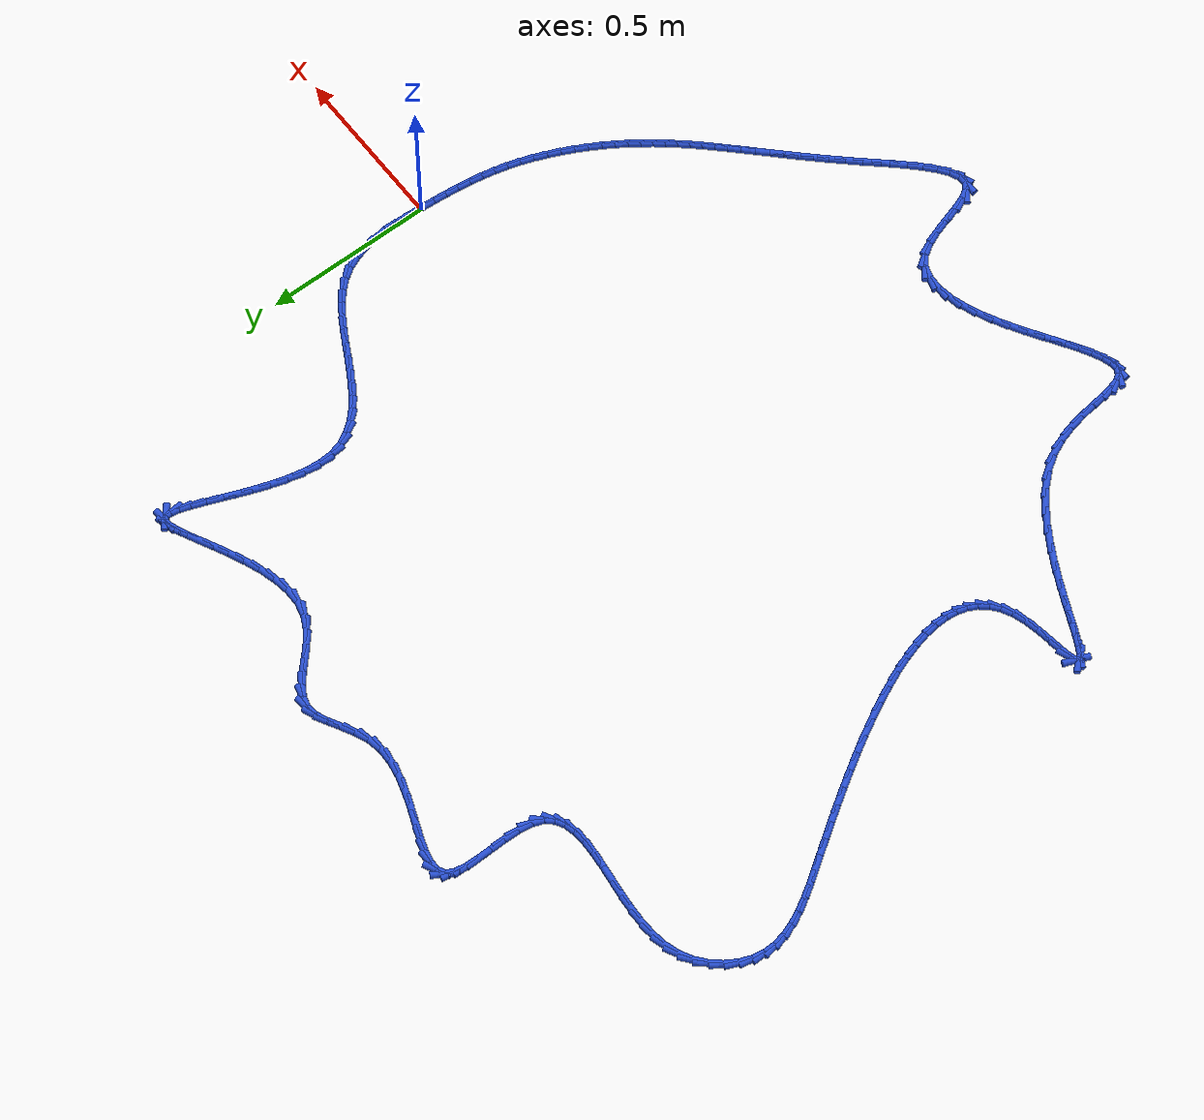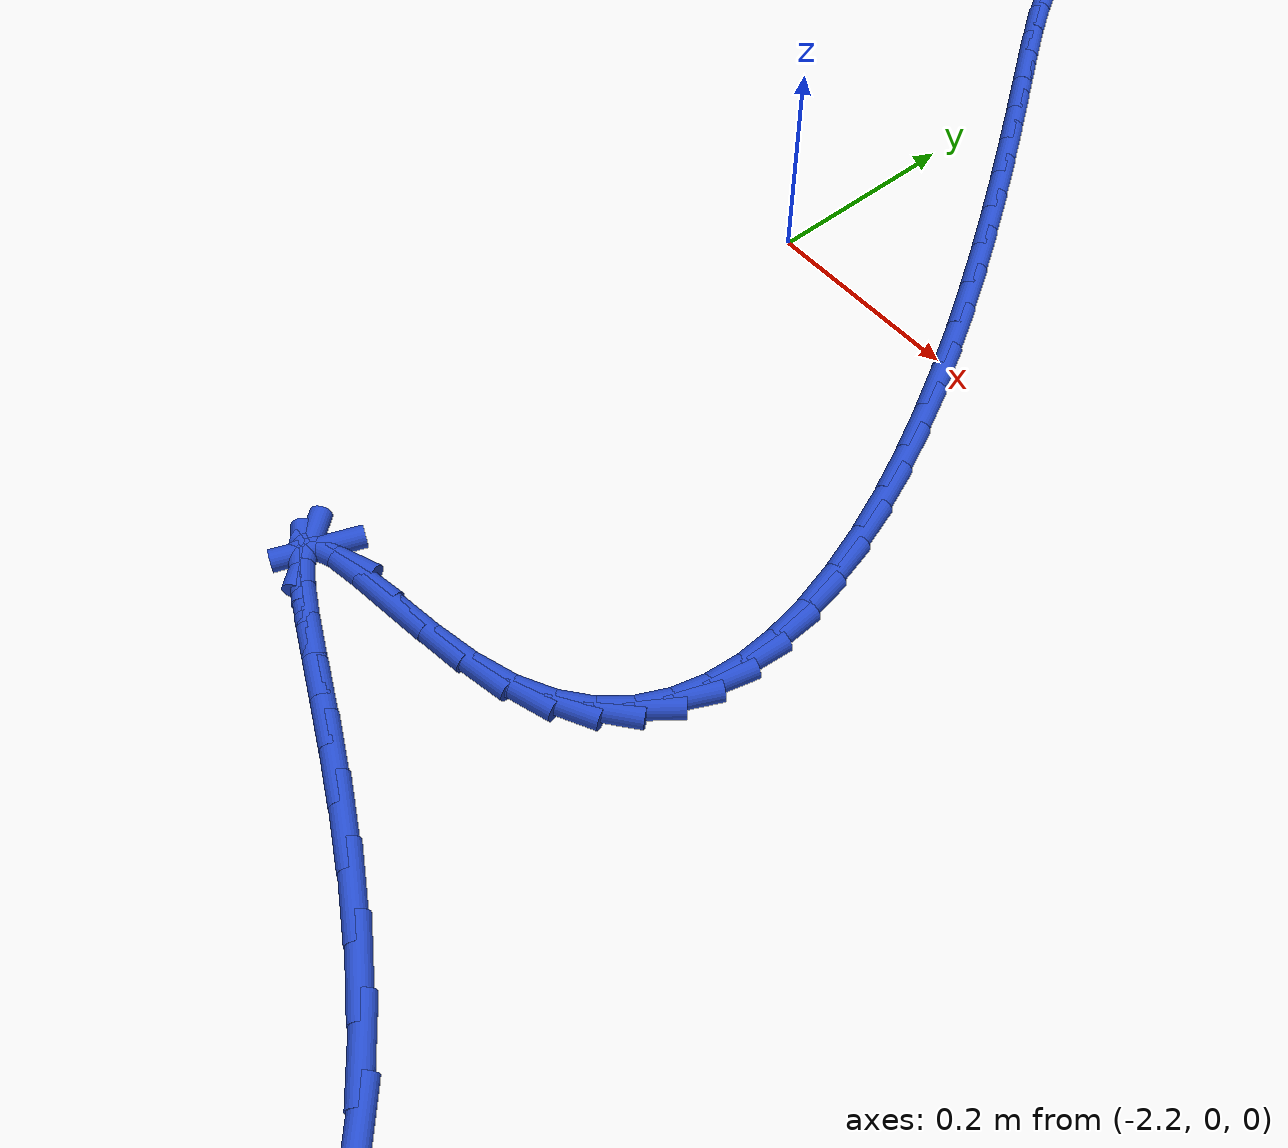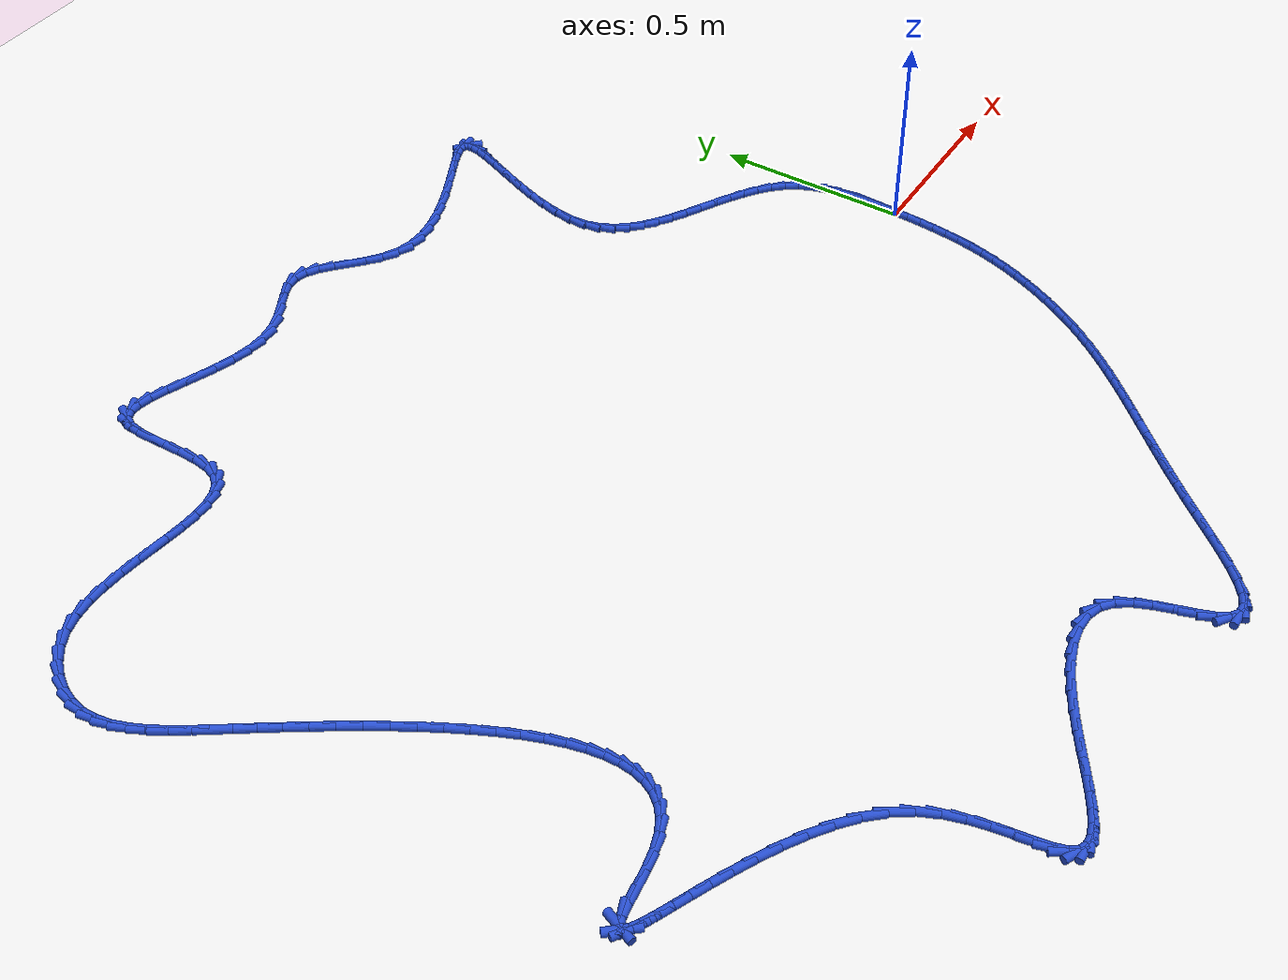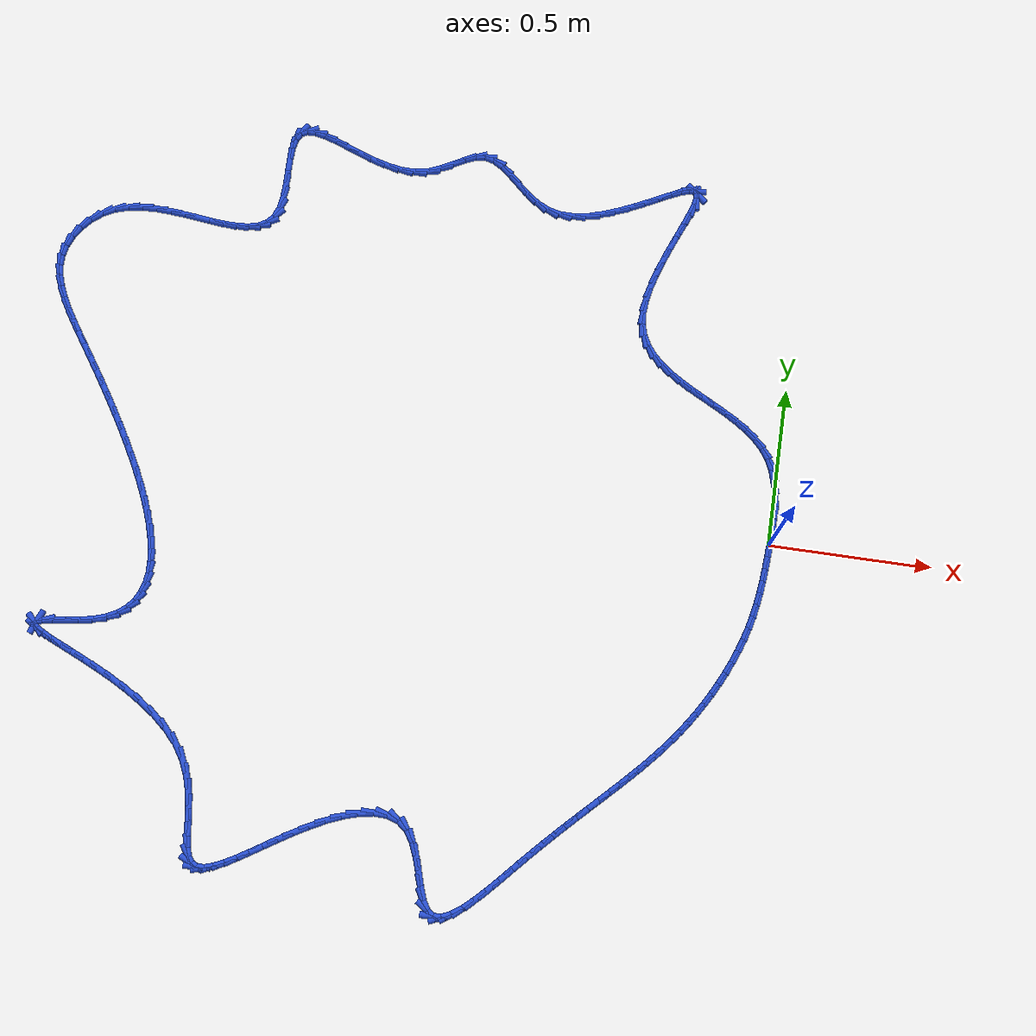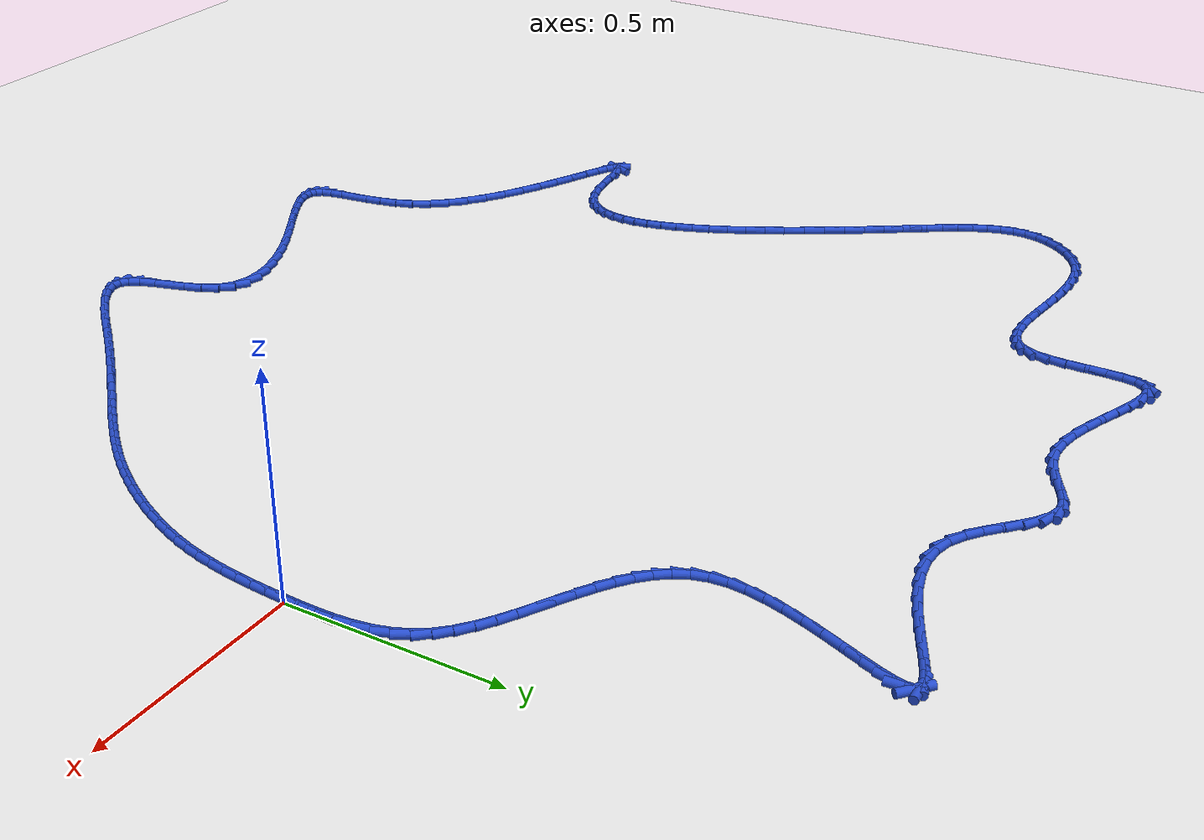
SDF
<sdf version="1.6">
 <world name="default">
  <light name="sun" type="directional">
   <pose>0 0 10 0 -0 0</pose>
   <diffuse>0.8 0.8 0.8 1</diffuse>
   <specular>0.2 0.2 0.2 1</specular>
   <attenuation>
    <range>1000</range>
    <constant>0.9</constant>
    <linear>0.01</linear>
    <quadratic>0.001</quadratic>
   </attenuation>
   <direction>-0.5 0.1 -0.9</direction>
  </light>
  <model name="ground_plane">
   <static>1</static>
   <link name="link">
    <collision name="collision">
     <geometry><plane><normal>0 0 1</normal><size>100 100</size></plane></geometry>
     <surface><friction><ode><mu>100</mu><mu2>50</mu2></ode></friction></surface>
    </collision>
    <visual name="visual">
     <cast_shadows>0</cast_shadows>
     <geometry><plane><normal>0 0 1</normal><size>100 100</size></plane></geometry>
     <material>
      <script><uri>file://media/materials/scripts/gazebo.material</uri><name>Gazebo/WhiteGlow</name></script>
     </material>
    </visual>
   </link>
  </model>
  <gravity>0 0 -9.8</gravity>
  <magnetic_field>6e-06 2.3e-05 -4.2e-05</magnetic_field>
  <atmosphere type="adiabatic"/>
  <physics name="default_physics" default="0" type="ode">
   <max_step_size>0.001</max_step_size>
   <real_time_factor>1</real_time_factor>
   <real_time_update_rate>1000</real_time_update_rate>
  </physics>
  <scene><ambient>0.4 0.4 0.4 1</ambient><background>0.7 0.7 0.7 1</background><shadows>1</shadows></scene>
  <spherical_coordinates>
   <surface_model>EARTH_WGS84</surface_model>
   <latitude_deg>0</latitude_deg>
   <longitude_deg>0</longitude_deg>
   <elevation>0</elevation>
   <heading_deg>0</heading_deg>
  </spherical_coordinates>
  <model name="line">
   <link name="link_0">
    <pose>-4.9439619065339e-17 -1.3877787807814457e-17 0.01 0 1.57 1.5212782375140808</pose>
    <collision name="collision">
     <geometry><cylinder><radius>0.01</radius><length>0.08</length></cylinder></geometry>
    </collision>
    <visual name="visual">
     <material>
      <script><name>Gazebo/Blue</name><uri>file://media/materials/scripts/gazebo.material</uri></script>
     </material>
     <geometry><cylinder><radius>0.01</radius><length>0.08</length></cylinder></geometry>
    </visual>
   </link>
   <link name="link_1">
    <pose>0.002019072190069594 0.0407411042475016 0.01 0 1.57 1.547509694619837</pose>
    <collision name="collision">
     <geometry><cylinder><radius>0.01</radius><length>0.08</length></cylinder></geometry>
    </collision>
    <visual name="visual">
     <material>
      <script><name>Gazebo/Blue</name><uri>file://media/materials/scripts/gazebo.material</uri></script>
     </material>
     <geometry><cylinder><radius>0.01</radius><length>0.08</length></cylinder></geometry>
    </visual>
   </link>
   <link name="link_2">
    <pose>0.00297402738892121 0.08174242087388409 0.01 0 1.57 -1.5500578191192729</pose>
    <collision name="collision">
     <geometry><cylinder><radius>0.01</radius><length>0.08</length></cylinder></geometry>
    </collision>
    <visual name="visual">
     <material>
      <script><name>Gazebo/Blue</name><uri>file://media/materials/scripts/gazebo.material</uri></script>
     </material>
     <geometry><cylinder><radius>0.01</radius><length>0.08</length></cylinder></geometry>
    </visual>
   </link>
   <link name="link_3">
    <pose>0.002130005010686799 0.12243490402226717 0.01 0 1.57 -1.4861592672072554</pose>
    <collision name="collision">
     <geometry><cylinder><radius>0.01</radius><length>0.08</length></cylinder></geometry>
    </collision>
    <visual name="visual">
     <material>
      <script><name>Gazebo/Blue</name><uri>file://media/materials/scripts/gazebo.material</uri></script>
     </material>
     <geometry><cylinder><radius>0.01</radius><length>0.08</length></cylinder></geometry>
    </visual>
   </link>
   <link name="link_4">
    <pose>-0.0012478555305016417 0.1622495078357706 0.01 0 1.57 -1.3992653829619528</pose>
    <collision name="collision">
     <geometry><cylinder><radius>0.01</radius><length>0.08</length></cylinder></geometry>
    </collision>
    <visual name="visual">
     <material>
      <script><name>Gazebo/Blue</name><uri>file://media/materials/scripts/gazebo.material</uri></script>
     </material>
     <geometry><cylinder><radius>0.01</radius><length>0.08</length></cylinder></geometry>
    </visual>
   </link>
   <link name="link_5">
    <pose>-0.007894414820512115 0.20061718645751414 0.01 0 1.57 -1.2857974622608102</pose>
    <collision name="collision">
     <geometry><cylinder><radius>0.01</radius><length>0.08</length></cylinder></geometry>
    </collision>
    <visual name="visual">
     <material>
      <script><name>Gazebo/Blue</name><uri>file://media/materials/scripts/gazebo.material</uri></script>
     </material>
     <geometry><cylinder><radius>0.01</radius><length>0.08</length></cylinder></geometry>
    </visual>
   </link>
   <link name="link_6">
    <pose>-0.018544533445212612 0.23696889403061752 0.01 0 1.57 -1.1431864656704414</pose>
    <collision name="collision">
     <geometry><cylinder><radius>0.01</radius><length>0.08</length></cylinder></geometry>
    </collision>
    <visual name="visual">
     <material>
      <script><name>Gazebo/Blue</name><uri>file://media/materials/scripts/gazebo.material</uri></script>
     </material>
     <geometry><cylinder><radius>0.01</radius><length>0.08</length></cylinder></geometry>
    </visual>
   </link>
   <link name="link_7">
    <pose>-0.033933071990471145 0.2707355846982004 0.01 0 1.57 -0.9750831358522055</pose>
    <collision name="collision">
     <geometry><cylinder><radius>0.01</radius><length>0.08</length></cylinder></geometry>
    </collision>
    <visual name="visual">
     <material>
      <script><name>Gazebo/Blue</name><uri>file://media/materials/scripts/gazebo.material</uri></script>
     </material>
     <geometry><cylinder><radius>0.01</radius><length>0.08</length></cylinder></geometry>
    </visual>
   </link>
   <link name="link_8">
    <pose>-0.0547186259004707 0.30139898726054243 0.01 0 1.57 -0.8180725574700213</pose>
    <collision name="collision">
     <geometry><cylinder><radius>0.01</radius><length>0.08</length></cylinder></geometry>
    </collision>
    <visual name="visual">
     <material>
      <script><name>Gazebo/Blue</name><uri>file://media/materials/scripts/gazebo.material</uri></script>
     </material>
     <geometry><cylinder><radius>0.01</radius><length>0.08</length></cylinder></geometry>
    </visual>
   </link>
   <link name="link_9">
    <pose>-0.08062906213488108 0.32906047690768675 0.01 0 1.57 -0.6958646833865341</pose>
    <collision name="collision">
     <geometry><cylinder><radius>0.01</radius><length>0.08</length></cylinder></geometry>
    </collision>
    <visual name="visual">
     <material>
      <script><name>Gazebo/Blue</name><uri>file://media/materials/scripts/gazebo.material</uri></script>
     </material>
     <geometry><cylinder><radius>0.01</radius><length>0.08</length></cylinder></geometry>
    </visual>
   </link>
   <link name="link_10">
    <pose>-0.11077012808983928 0.35423561422096833 0.01 0 1.57 -0.6064150932091392</pose>
    <collision name="collision">
     <geometry><cylinder><radius>0.01</radius><length>0.08</length></cylinder></geometry>
    </collision>
    <visual name="visual">
     <material>
      <script><name>Gazebo/Blue</name><uri>file://media/materials/scripts/gazebo.material</uri></script>
     </material>
     <geometry><cylinder><radius>0.01</radius><length>0.08</length></cylinder></geometry>
    </visual>
   </link>
   <link name="link_11">
    <pose>-0.14423618496678628 0.37744754031090344 0.01 0 1.57 -0.5453350447290717</pose>
    <collision name="collision">
     <geometry><cylinder><radius>0.01</radius><length>0.08</length></cylinder></geometry>
    </collision>
    <visual name="visual">
     <material>
      <script><name>Gazebo/Blue</name><uri>file://media/materials/scripts/gazebo.material</uri></script>
     </material>
     <geometry><cylinder><radius>0.01</radius><length>0.08</length></cylinder></geometry>
    </visual>
   </link>
   <link name="link_12">
    <pose>-0.180121593967163 0.3992193962880084 0.01 0 1.57 -0.5086834063708454</pose>
    <collision name="collision">
     <geometry><cylinder><radius>0.01</radius><length>0.08</length></cylinder></geometry>
    </collision>
    <visual name="visual">
     <material>
      <script><name>Gazebo/Blue</name><uri>file://media/materials/scripts/gazebo.material</uri></script>
     </material>
     <geometry><cylinder><radius>0.01</radius><length>0.08</length></cylinder></geometry>
    </visual>
   </link>
   <link name="link_13">
    <pose>-0.21752071629241038 0.42007432326279925 0.01 0 1.57 -0.4938541760679135</pose>
    <collision name="collision">
     <geometry><cylinder><radius>0.01</radius><length>0.08</length></cylinder></geometry>
    </collision>
    <visual name="visual">
     <material>
      <script><name>Gazebo/Blue</name><uri>file://media/materials/scripts/gazebo.material</uri></script>
     </material>
     <geometry><cylinder><radius>0.01</radius><length>0.08</length></cylinder></geometry>
    </visual>
   </link>
   <link name="link_14">
    <pose>-0.2555279131439692 0.44053546234579233 0.01 0 1.57 -0.4997881079672558</pose>
    <collision name="collision">
     <geometry><cylinder><radius>0.01</radius><length>0.08</length></cylinder></geometry>
    </collision>
    <visual name="visual">
     <material>
      <script><name>Gazebo/Blue</name><uri>file://media/materials/scripts/gazebo.material</uri></script>
     </material>
     <geometry><cylinder><radius>0.01</radius><length>0.08</length></cylinder></geometry>
    </visual>
   </link>
   <link name="link_15">
    <pose>-0.2932375457232807 0.46112595464750383 0.01 0 1.57 -0.5270022086999685</pose>
    <collision name="collision">
     <geometry><cylinder><radius>0.01</radius><length>0.08</length></cylinder></geometry>
    </collision>
    <visual name="visual">
     <material>
      <script><name>Gazebo/Blue</name><uri>file://media/materials/scripts/gazebo.material</uri></script>
     </material>
     <geometry><cylinder><radius>0.01</radius><length>0.08</length></cylinder></geometry>
    </visual>
   </link>
   <link name="link_16">
    <pose>-0.32974397523178556 0.48236894127845 0.01 0 1.57 -0.5776043497219896</pose>
    <collision name="collision">
     <geometry><cylinder><radius>0.01</radius><length>0.08</length></cylinder></geometry>
    </collision>
    <visual name="visual">
     <material>
      <script><name>Gazebo/Blue</name><uri>file://media/materials/scripts/gazebo.material</uri></script>
     </material>
     <geometry><cylinder><radius>0.01</radius><length>0.08</length></cylinder></geometry>
    </visual>
   </link>
   <link name="link_17">
    <pose>-0.36414156287092464 0.5047875633491468 0.01 0 1.57 -0.6552259573490895</pose>
    <collision name="collision">
     <geometry><cylinder><radius>0.01</radius><length>0.08</length></cylinder></geometry>
    </collision>
    <visual name="visual">
     <material>
      <script><name>Gazebo/Blue</name><uri>file://media/materials/scripts/gazebo.material</uri></script>
     </material>
     <geometry><cylinder><radius>0.01</radius><length>0.08</length></cylinder></geometry>
    </visual>
   </link>
   <link name="link_18">
    <pose>-0.39552466984213913 0.5289049619701107 0.01 0 1.57 -0.7645160113666479</pose>
    <collision name="collision">
     <geometry><cylinder><radius>0.01</radius><length>0.08</length></cylinder></geometry>
    </collision>
    <visual name="visual">
     <material>
      <script><name>Gazebo/Blue</name><uri>file://media/materials/scripts/gazebo.material</uri></script>
     </material>
     <geometry><cylinder><radius>0.01</radius><length>0.08</length></cylinder></geometry>
    </visual>
   </link>
   <link name="link_19">
    <pose>-0.4229876573468699 0.5552442782518581 0.01 0 1.57 -0.90940943849488</pose>
    <collision name="collision">
     <geometry><cylinder><radius>0.01</radius><length>0.08</length></cylinder></geometry>
    </collision>
    <visual name="visual">
     <material>
      <script><name>Gazebo/Blue</name><uri>file://media/materials/scripts/gazebo.material</uri></script>
     </material>
     <geometry><cylinder><radius>0.01</radius><length>0.08</length></cylinder></geometry>
    </visual>
   </link>
   <link name="link_20">
    <pose>-0.44562488658655774 0.5843286533049047 0.01 0 1.57 -1.0892720307665782</pose>
    <collision name="collision">
     <geometry><cylinder><radius>0.01</radius><length>0.08</length></cylinder></geometry>
    </collision>
    <visual name="visual">
     <material>
      <script><name>Gazebo/Blue</name><uri>file://media/materials/scripts/gazebo.material</uri></script>
     </material>
     <geometry><cylinder><radius>0.01</radius><length>0.08</length></cylinder></geometry>
    </visual>
   </link>
   <link name="link_21">
    <pose>-0.46253071876264346 0.6166812282397668 0.01 0 1.57 -1.2939818250842174</pose>
    <collision name="collision">
     <geometry><cylinder><radius>0.01</radius><length>0.08</length></cylinder></geometry>
    </collision>
    <visual name="visual">
     <material>
      <script><name>Gazebo/Blue</name><uri>file://media/materials/scripts/gazebo.material</uri></script>
     </material>
     <geometry><cylinder><radius>0.01</radius><length>0.08</length></cylinder></geometry>
    </visual>
   </link>
   <link name="link_22">
    <pose>-0.4727995150765682 0.6528251441669608 0.01 0 1.57 -1.4990107906677212</pose>
    <collision name="collision">
     <geometry><cylinder><radius>0.01</radius><length>0.08</length></cylinder></geometry>
    </collision>
    <visual name="visual">
     <material>
      <script><name>Gazebo/Blue</name><uri>file://media/materials/scripts/gazebo.material</uri></script>
     </material>
     <geometry><cylinder><radius>0.01</radius><length>0.08</length></cylinder></geometry>
    </visual>
   </link>
   <link name="link_23">
    <pose>-0.47569950325526184 0.6931536734492194 0.01 0 1.57 1.4840365722013258</pose>
    <collision name="collision">
     <geometry><cylinder><radius>0.01</radius><length>0.08</length></cylinder></geometry>
    </collision>
    <visual name="visual">
     <material>
      <script><name>Gazebo/Blue</name><uri>file://media/materials/scripts/gazebo.material</uri></script>
     </material>
     <geometry><cylinder><radius>0.01</radius><length>0.08</length></cylinder></geometry>
    </visual>
   </link>
   <link name="link_24">
    <pose>-0.4718835881320104 0.7370258106814196 0.01 0 1.57 1.3742121819596693</pose>
    <collision name="collision">
     <geometry><cylinder><radius>0.01</radius><length>0.08</length></cylinder></geometry>
    </collision>
    <visual name="visual">
     <material>
      <script><name>Gazebo/Blue</name><uri>file://media/materials/scripts/gazebo.material</uri></script>
     </material>
     <geometry><cylinder><radius>0.01</radius><length>0.08</length></cylinder></geometry>
    </visual>
   </link>
   <link name="link_25">
    <pose>-0.46266656815177026 0.7833061522741295 0.01 0 1.57 1.2980764402193847</pose>
    <collision name="collision">
     <geometry><cylinder><radius>0.01</radius><length>0.08</length></cylinder></geometry>
    </collision>
    <visual name="visual">
     <material>
      <script><name>Gazebo/Blue</name><uri>file://media/materials/scripts/gazebo.material</uri></script>
     </material>
     <geometry><cylinder><radius>0.01</radius><length>0.08</length></cylinder></geometry>
    </visual>
   </link>
   <link name="link_26">
    <pose>-0.44936735789052773 0.8308562201140498 0.01 0 1.57 1.2458646300318095</pose>
    <collision name="collision">
     <geometry><cylinder><radius>0.01</radius><length>0.08</length></cylinder></geometry>
    </collision>
    <visual name="visual">
     <material>
      <script><name>Gazebo/Blue</name><uri>file://media/materials/scripts/gazebo.material</uri></script>
     </material>
     <geometry><cylinder><radius>0.01</radius><length>0.08</length></cylinder></geometry>
    </visual>
   </link>
   <link name="link_27">
    <pose>-0.4333048719242693 0.8785375360878804 0.01 0 1.57 1.211949305810879</pose>
    <collision name="collision">
     <geometry><cylinder><radius>0.01</radius><length>0.08</length></cylinder></geometry>
    </collision>
    <visual name="visual">
     <material>
      <script><name>Gazebo/Blue</name><uri>file://media/materials/scripts/gazebo.material</uri></script>
     </material>
     <geometry><cylinder><radius>0.01</radius><length>0.08</length></cylinder></geometry>
    </visual>
   </link>
   <link name="link_28">
    <pose>-0.41579802482898115 0.9252116220823217 0.01 0 1.57 1.193761300913318</pose>
    <collision name="collision">
     <geometry><cylinder><radius>0.01</radius><length>0.08</length></cylinder></geometry>
    </collision>
    <visual name="visual">
     <material>
      <script><name>Gazebo/Blue</name><uri>file://media/materials/scripts/gazebo.material</uri></script>
     </material>
     <geometry><cylinder><radius>0.01</radius><length>0.08</length></cylinder></geometry>
    </visual>
   </link>
   <link name="link_29">
    <pose>-0.3981657311806492 0.9697399999840737 0.01 0 1.57 1.191520634864494</pose>
    <collision name="collision">
     <geometry><cylinder><radius>0.01</radius><length>0.08</length></cylinder></geometry>
    </collision>
    <visual name="visual">
     <material>
      <script><name>Gazebo/Blue</name><uri>file://media/materials/scripts/gazebo.material</uri></script>
     </material>
     <geometry><cylinder><radius>0.01</radius><length>0.08</length></cylinder></geometry>
    </visual>
   </link>
   <link name="link_30">
    <pose>-0.38172690555526 1.0109841916798368 0.01 0 1.57 1.2092102701060599</pose>
    <collision name="collision">
     <geometry><cylinder><radius>0.01</radius><length>0.08</length></cylinder></geometry>
    </collision>
    <visual name="visual">
     <material>
      <script><name>Gazebo/Blue</name><uri>file://media/materials/scripts/gazebo.material</uri></script>
     </material>
     <geometry><cylinder><radius>0.01</radius><length>0.08</length></cylinder></geometry>
    </visual>
   </link>
   <link name="link_31">
    <pose>-0.3678004625287998 1.0478057190563108 0.01 0 1.57 1.2584311544003208</pose>
    <collision name="collision">
     <geometry><cylinder><radius>0.01</radius><length>0.08</length></cylinder></geometry>
    </collision>
    <visual name="visual">
     <material>
      <script><name>Gazebo/Blue</name><uri>file://media/materials/scripts/gazebo.material</uri></script>
     </material>
     <geometry><cylinder><radius>0.01</radius><length>0.08</length></cylinder></geometry>
    </visual>
   </link>
   <link name="link_32">
    <pose>-0.35770531667725475 1.079066104000196 0.01 0 1.57 1.3721177328059906</pose>
    <collision name="collision">
     <geometry><cylinder><radius>0.01</radius><length>0.08</length></cylinder></geometry>
    </collision>
    <visual name="visual">
     <material>
      <script><name>Gazebo/Blue</name><uri>file://media/materials/scripts/gazebo.material</uri></script>
     </material>
     <geometry><cylinder><radius>0.01</radius><length>0.08</length></cylinder></geometry>
    </visual>
   </link>
   <link name="link_33">
    <pose>-0.3527603825766111 1.1036268683981927 0.01 0 1.57 -1.4799021810856055</pose>
    <collision name="collision">
     <geometry><cylinder><radius>0.01</radius><length>0.08</length></cylinder></geometry>
    </collision>
    <visual name="visual">
     <material>
      <script><name>Gazebo/Blue</name><uri>file://media/materials/scripts/gazebo.material</uri></script>
     </material>
     <geometry><cylinder><radius>0.01</radius><length>0.08</length></cylinder></geometry>
    </visual>
   </link>
   <link name="link_34">
    <pose>-0.35428457480285513 1.1203495341370011 0.01 0 1.57 -0.697594900266382</pose>
    <collision name="collision">
     <geometry><cylinder><radius>0.01</radius><length>0.08</length></cylinder></geometry>
    </collision>
    <visual name="visual">
     <material>
      <script><name>Gazebo/Blue</name><uri>file://media/materials/scripts/gazebo.material</uri></script>
     </material>
     <geometry><cylinder><radius>0.01</radius><length>0.08</length></cylinder></geometry>
    </visual>
   </link>
   <link name="link_35">
    <pose>-0.3635677668057536 1.128130569094776 0.01 0 1.57 0.061412992556619694</pose>
    <collision name="collision">
     <geometry><cylinder><radius>0.01</radius><length>0.08</length></cylinder></geometry>
    </collision>
    <visual name="visual">
     <material>
      <script><name>Gazebo/Blue</name><uri>file://media/materials/scripts/gazebo.material</uri></script>
     </material>
     <geometry><cylinder><radius>0.01</radius><length>0.08</length></cylinder></geometry>
    </visual>
   </link>
   <link name="link_36">
    <pose>-0.3809041705947366 1.1270645481350383 0.01 0 1.57 0.3289009638198146</pose>
    <collision name="collision">
     <geometry><cylinder><radius>0.01</radius><length>0.08</length></cylinder></geometry>
    </collision>
    <visual name="visual">
     <material>
      <script><name>Gazebo/Blue</name><uri>file://media/materials/scripts/gazebo.material</uri></script>
     </material>
     <geometry><cylinder><radius>0.01</radius><length>0.08</length></cylinder></geometry>
    </visual>
   </link>
   <link name="link_37">
    <pose>-0.40536683500557974 1.1187155055874975 0.01 0 1.57 0.42865265110448636</pose>
    <collision name="collision">
     <geometry><cylinder><radius>0.01</radius><length>0.08</length></cylinder></geometry>
    </collision>
    <visual name="visual">
     <material>
      <script><name>Gazebo/Blue</name><uri>file://media/materials/scripts/gazebo.material</uri></script>
     </material>
     <geometry><cylinder><radius>0.01</radius><length>0.08</length></cylinder></geometry>
    </visual>
   </link>
   <link name="link_38">
    <pose>-0.435954077342247 1.1047374023037362 0.01 0 1.57 0.4658436570741813</pose>
    <collision name="collision">
     <geometry><cylinder><radius>0.01</radius><length>0.08</length></cylinder></geometry>
    </collision>
    <visual name="visual">
     <material>
      <script><name>Gazebo/Blue</name><uri>file://media/materials/scripts/gazebo.material</uri></script>
     </material>
     <geometry><cylinder><radius>0.01</radius><length>0.08</length></cylinder></geometry>
    </visual>
   </link>
   <link name="link_39">
    <pose>-0.4716642149087021 1.0867841991353362 0.01 0 1.57 0.47082534776931784</pose>
    <collision name="collision">
     <geometry><cylinder><radius>0.01</radius><length>0.08</length></cylinder></geometry>
    </collision>
    <visual name="visual">
     <material>
      <script><name>Gazebo/Blue</name><uri>file://media/materials/scripts/gazebo.material</uri></script>
     </material>
     <geometry><cylinder><radius>0.01</radius><length>0.08</length></cylinder></geometry>
    </visual>
   </link>
   <link name="link_40">
    <pose>-0.5114955650089086 1.06650985693388 0.01 0 1.57 0.4536534978455763</pose>
    <collision name="collision">
     <geometry><cylinder><radius>0.01</radius><length>0.08</length></cylinder></geometry>
    </collision>
    <visual name="visual">
     <material>
      <script><name>Gazebo/Blue</name><uri>file://media/materials/scripts/gazebo.material</uri></script>
     </material>
     <geometry><cylinder><radius>0.01</radius><length>0.08</length></cylinder></geometry>
    </visual>
   </link>
   <link name="link_41">
    <pose>-0.5544464449468299 1.04556833655095 0.01 0 1.57 0.4168188583055822</pose>
    <collision name="collision">
     <geometry><cylinder><radius>0.01</radius><length>0.08</length></cylinder></geometry>
    </collision>
    <visual name="visual">
     <material>
      <script><name>Gazebo/Blue</name><uri>file://media/materials/scripts/gazebo.material</uri></script>
     </material>
     <geometry><cylinder><radius>0.01</radius><length>0.08</length></cylinder></geometry>
    </visual>
   </link>
   <link name="link_42">
    <pose>-0.5995151720264303 1.0256135988381283 0.01 0 1.57 0.3586692965020733</pose>
    <collision name="collision">
     <geometry><cylinder><radius>0.01</radius><length>0.08</length></cylinder></geometry>
    </collision>
    <visual name="visual">
     <material>
      <script><name>Gazebo/Blue</name><uri>file://media/materials/scripts/gazebo.material</uri></script>
     </material>
     <geometry><cylinder><radius>0.01</radius><length>0.08</length></cylinder></geometry>
    </visual>
   </link>
   <link name="link_43">
    <pose>-0.6457000635516732 1.0082996046469967 0.01 0 1.57 0.27411923524427345</pose>
    <collision name="collision">
     <geometry><cylinder><radius>0.01</radius><length>0.08</length></cylinder></geometry>
    </collision>
    <visual name="visual">
     <material>
      <script><name>Gazebo/Blue</name><uri>file://media/materials/scripts/gazebo.material</uri></script>
     </material>
     <geometry><cylinder><radius>0.01</radius><length>0.08</length></cylinder></geometry>
    </visual>
   </link>
   <link name="link_44">
    <pose>-0.6919994368265221 0.9952803148291377 0.01 0 1.57 0.15445871595914</pose>
    <collision name="collision">
     <geometry><cylinder><radius>0.01</radius><length>0.08</length></cylinder></geometry>
    </collision>
    <visual name="visual">
     <material>
      <script><name>Gazebo/Blue</name><uri>file://media/materials/scripts/gazebo.material</uri></script>
     </material>
     <geometry><cylinder><radius>0.01</radius><length>0.08</length></cylinder></geometry>
    </visual>
   </link>
   <link name="link_45">
    <pose>-0.7374116091549409 0.9882096902361333 0.01 0 1.57 -0.012222766391572677</pose>
    <collision name="collision">
     <geometry><cylinder><radius>0.01</radius><length>0.08</length></cylinder></geometry>
    </collision>
    <visual name="visual">
     <material>
      <script><name>Gazebo/Blue</name><uri>file://media/materials/scripts/gazebo.material</uri></script>
     </material>
     <geometry><cylinder><radius>0.01</radius><length>0.08</length></cylinder></geometry>
    </visual>
   </link>
   <link name="link_46">
    <pose>-0.7809348978408933 0.9887416917195663 0.01 0 1.57 -0.2361194447221591</pose>
    <collision name="collision">
     <geometry><cylinder><radius>0.01</radius><length>0.08</length></cylinder></geometry>
    </collision>
    <visual name="visual">
     <material>
      <script><name>Gazebo/Blue</name><uri>file://media/materials/scripts/gazebo.material</uri></script>
     </material>
     <geometry><cylinder><radius>0.01</radius><length>0.08</length></cylinder></geometry>
    </visual>
   </link>
   <link name="link_47">
    <pose>-0.8215713661423033 0.998519136332389 0.01 0 1.57 -0.47446259756762127</pose>
    <collision name="collision">
     <geometry><cylinder><radius>0.01</radius><length>0.08</length></cylinder></geometry>
    </collision>
    <visual name="visual">
     <material>
      <script><name>Gazebo/Blue</name><uri>file://media/materials/scripts/gazebo.material</uri></script>
     </material>
     <geometry><cylinder><radius>0.01</radius><length>0.08</length></cylinder></geometry>
    </visual>
   </link>
   <link name="link_48">
    <pose>-0.8588362780828055 1.017658125623272 0.01 0 1.57 -0.6382949397071945</pose>
    <collision name="collision">
     <geometry><cylinder><radius>0.01</radius><length>0.08</length></cylinder></geometry>
    </collision>
    <visual name="visual">
     <material>
      <script><name>Gazebo/Blue</name><uri>file://media/materials/scripts/gazebo.material</uri></script>
     </material>
     <geometry><cylinder><radius>0.01</radius><length>0.08</length></cylinder></geometry>
    </visual>
   </link>
   <link name="link_49">
    <pose>-0.8932755954412324 1.0432085493418637 0.01 0 1.57 -0.7257580335973369</pose>
    <collision name="collision">
     <geometry><cylinder><radius>0.01</radius><length>0.08</length></cylinder></geometry>
    </collision>
    <visual name="visual">
     <material>
      <script><name>Gazebo/Blue</name><uri>file://media/materials/scripts/gazebo.material</uri></script>
     </material>
     <geometry><cylinder><radius>0.01</radius><length>0.08</length></cylinder></geometry>
    </visual>
   </link>
   <link name="link_50">
    <pose>-0.9255585857476128 1.0718534762689127 0.01 0 1.57 -0.7453403258176318</pose>
    <collision name="collision">
     <geometry><cylinder><radius>0.01</radius><length>0.08</length></cylinder></geometry>
    </collision>
    <visual name="visual">
     <material>
      <script><name>Gazebo/Blue</name><uri>file://media/materials/scripts/gazebo.material</uri></script>
     </material>
     <geometry><cylinder><radius>0.01</radius><length>0.08</length></cylinder></geometry>
    </visual>
   </link>
   <link name="link_51">
    <pose>-0.9563545165319753 1.1002759751851665 0.01 0 1.57 -0.6927932049309159</pose>
    <collision name="collision">
     <geometry><cylinder><radius>0.01</radius><length>0.08</length></cylinder></geometry>
    </collision>
    <visual name="visual">
     <material>
      <script><name>Gazebo/Blue</name><uri>file://media/materials/scripts/gazebo.material</uri></script>
     </material>
     <geometry><cylinder><radius>0.01</radius><length>0.08</length></cylinder></geometry>
    </visual>
   </link>
   <link name="link_52">
    <pose>-0.986332655324349 1.1251591148713742 0.01 0 1.57 -0.5435952391287627</pose>
    <collision name="collision">
     <geometry><cylinder><radius>0.01</radius><length>0.08</length></cylinder></geometry>
    </collision>
    <visual name="visual">
     <material>
      <script><name>Gazebo/Blue</name><uri>file://media/materials/scripts/gazebo.material</uri></script>
     </material>
     <geometry><cylinder><radius>0.01</radius><length>0.08</length></cylinder></geometry>
    </visual>
   </link>
   <link name="link_53">
    <pose>-1.0161622696547623 1.143185964108283 0.01 0 1.57 -0.2532114460902516</pose>
    <collision name="collision">
     <geometry><cylinder><radius>0.01</radius><length>0.08</length></cylinder></geometry>
    </collision>
    <visual name="visual">
     <material>
      <script><name>Gazebo/Blue</name><uri>file://media/materials/scripts/gazebo.material</uri></script>
     </material>
     <geometry><cylinder><radius>0.01</radius><length>0.08</length></cylinder></geometry>
    </visual>
   </link>
   <link name="link_54">
    <pose>-1.0465126270532437 1.1510395916766412 0.01 0 1.57 0.1453605776418237</pose>
    <collision name="collision">
     <geometry><cylinder><radius>0.01</radius><length>0.08</length></cylinder></geometry>
    </collision>
    <visual name="visual">
     <material>
      <script><name>Gazebo/Blue</name><uri>file://media/materials/scripts/gazebo.material</uri></script>
     </material>
     <geometry><cylinder><radius>0.01</radius><length>0.08</length></cylinder></geometry>
    </visual>
   </link>
   <link name="link_55">
    <pose>-1.0780071121308081 1.1464290159405894 0.01 0 1.57 0.4064266854414274</pose>
    <collision name="collision">
     <geometry><cylinder><radius>0.01</radius><length>0.08</length></cylinder></geometry>
    </collision>
    <visual name="visual">
     <material>
      <script><name>Gazebo/Blue</name><uri>file://media/materials/scripts/gazebo.material</uri></script>
     </material>
     <geometry><cylinder><radius>0.01</radius><length>0.08</length></cylinder></geometry>
    </visual>
   </link>
   <link name="link_56">
    <pose>-1.1110388222185321 1.132212516557784 0.01 0 1.57 0.5064151715837497</pose>
    <collision name="collision">
     <geometry><cylinder><radius>0.01</radius><length>0.08</length></cylinder></geometry>
    </collision>
    <visual name="visual">
     <material>
      <script><name>Gazebo/Blue</name><uri>file://media/materials/scripts/gazebo.material</uri></script>
     </material>
     <geometry><cylinder><radius>0.01</radius><length>0.08</length></cylinder></geometry>
    </visual>
   </link>
   <link name="link_57">
    <pose>-1.14592876070842 1.1128604054703723 0.01 0 1.57 0.49512315362481224</pose>
    <collision name="collision">
     <geometry><cylinder><radius>0.01</radius><length>0.08</length></cylinder></geometry>
    </collision>
    <visual name="visual">
     <material>
      <script><name>Gazebo/Blue</name><uri>file://media/materials/scripts/gazebo.material</uri></script>
     </material>
     <geometry><cylinder><radius>0.01</radius><length>0.08</length></cylinder></geometry>
    </visual>
   </link>
   <link name="link_58">
    <pose>-1.1829979061100724 1.092843550995067 0.01 0 1.57 0.38882251743181706</pose>
    <collision name="collision">
     <geometry><cylinder><radius>0.01</radius><length>0.08</length></cylinder></geometry>
    </collision>
    <visual name="visual">
     <material>
      <script><name>Gazebo/Blue</name><uri>file://media/materials/scripts/gazebo.material</uri></script>
     </material>
     <geometry><cylinder><radius>0.01</radius><length>0.08</length></cylinder></geometry>
    </visual>
   </link>
   <link name="link_59">
    <pose>-1.2225672369330933 1.0766328214485796 0.01 0 1.57 0.18886843430079545</pose>
    <collision name="collision">
     <geometry><cylinder><radius>0.01</radius><length>0.08</length></cylinder></geometry>
    </collision>
    <visual name="visual">
     <material>
      <script><name>Gazebo/Blue</name><uri>file://media/materials/scripts/gazebo.material</uri></script>
     </material>
     <geometry><cylinder><radius>0.01</radius><length>0.08</length></cylinder></geometry>
    </visual>
   </link>
   <link name="link_60">
    <pose>-1.2649243204528209 1.068536405833244 0.01 0 1.57 -0.02352594420173727</pose>
    <collision name="collision">
     <geometry><cylinder><radius>0.01</radius><length>0.08</length></cylinder></geometry>
    </collision>
    <visual name="visual">
     <material>
      <script><name>Gazebo/Blue</name><uri>file://media/materials/scripts/gazebo.material</uri></script>
     </material>
     <geometry><cylinder><radius>0.01</radius><length>0.08</length></cylinder></geometry>
    </visual>
   </link>
   <link name="link_61">
    <pose>-1.3096845394527534 1.0695896265637743 0.01 0 1.57 -0.1759563586497165</pose>
    <collision name="collision">
     <geometry><cylinder><radius>0.01</radius><length>0.08</length></cylinder></geometry>
    </collision>
    <visual name="visual">
     <material>
      <script><name>Gazebo/Blue</name><uri>file://media/materials/scripts/gazebo.material</uri></script>
     </material>
     <geometry><cylinder><radius>0.01</radius><length>0.08</length></cylinder></geometry>
    </visual>
   </link>
   <link name="link_62">
    <pose>-1.3558405898408972 1.0777959433831446 0.01 0 1.57 -0.27743981206993373</pose>
    <collision name="collision">
     <geometry><cylinder><radius>0.01</radius><length>0.08</length></cylinder></geometry>
    </collision>
    <visual name="visual">
     <material>
      <script><name>Gazebo/Blue</name><uri>file://media/materials/scripts/gazebo.material</uri></script>
     </material>
     <geometry><cylinder><radius>0.01</radius><length>0.08</length></cylinder></geometry>
    </visual>
   </link>
   <link name="link_63">
    <pose>-1.4023616739739386 1.091044425922567 0.01 0 1.57 -0.3392050994815514</pose>
    <collision name="collision">
     <geometry><cylinder><radius>0.01</radius><length>0.08</length></cylinder></geometry>
    </collision>
    <visual name="visual">
     <material>
      <script><name>Gazebo/Blue</name><uri>file://media/materials/scripts/gazebo.material</uri></script>
     </material>
     <geometry><cylinder><radius>0.01</radius><length>0.08</length></cylinder></geometry>
    </visual>
   </link>
   <link name="link_64">
    <pose>-1.4482169942085614 1.107224143813251 0.01 0 1.57 -0.36748716285291777</pose>
    <collision name="collision">
     <geometry><cylinder><radius>0.01</radius><length>0.08</length></cylinder></geometry>
    </collision>
    <visual name="visual">
     <material>
      <script><name>Gazebo/Blue</name><uri>file://media/materials/scripts/gazebo.material</uri></script>
     </material>
     <geometry><cylinder><radius>0.01</radius><length>0.08</length></cylinder></geometry>
    </visual>
   </link>
   <link name="link_65">
    <pose>-1.4923757529014512 1.1242241666864081 0.01 0 1.57 -0.36241845271144185</pose>
    <collision name="collision">
     <geometry><cylinder><radius>0.01</radius><length>0.08</length></cylinder></geometry>
    </collision>
    <visual name="visual">
     <material>
      <script><name>Gazebo/Blue</name><uri>file://media/materials/scripts/gazebo.material</uri></script>
     </material>
     <geometry><cylinder><radius>0.01</radius><length>0.08</length></cylinder></geometry>
    </visual>
   </link>
   <link name="link_66">
    <pose>-1.5338071524092933 1.1399335641732482 0.01 0 1.57 -0.31576856222250815</pose>
    <collision name="collision">
     <geometry><cylinder><radius>0.01</radius><length>0.08</length></cylinder></geometry>
    </collision>
    <visual name="visual">
     <material>
      <script><name>Gazebo/Blue</name><uri>file://media/materials/scripts/gazebo.material</uri></script>
     </material>
     <geometry><cylinder><radius>0.01</radius><length>0.08</length></cylinder></geometry>
    </visual>
   </link>
   <link name="link_67">
    <pose>-1.5714803950887712 1.1522414059049817 0.01 0 1.57 -0.20377621307233781</pose>
    <collision name="collision">
     <geometry><cylinder><radius>0.01</radius><length>0.08</length></cylinder></geometry>
    </collision>
    <visual name="visual">
     <material>
      <script><name>Gazebo/Blue</name><uri>file://media/materials/scripts/gazebo.material</uri></script>
     </material>
     <geometry><cylinder><radius>0.01</radius><length>0.08</length></cylinder></geometry>
    </visual>
   </link>
   <link name="link_68">
    <pose>-1.604364683296572 1.1590367615128192 0.01 0 1.57 0.030586249244087038</pose>
    <collision name="collision">
     <geometry><cylinder><radius>0.01</radius><length>0.08</length></cylinder></geometry>
    </collision>
    <visual name="visual">
     <material>
      <script><name>Gazebo/Blue</name><uri>file://media/materials/scripts/gazebo.material</uri></script>
     </material>
     <geometry><cylinder><radius>0.01</radius><length>0.08</length></cylinder></geometry>
    </visual>
   </link>
   <link name="link_69">
    <pose>-1.6314292193893785 1.158208700627971 0.01 0 1.57 0.48150847401066266</pose>
    <collision name="collision">
     <geometry><cylinder><radius>0.01</radius><length>0.08</length></cylinder></geometry>
    </collision>
    <visual name="visual">
     <material>
      <script><name>Gazebo/Blue</name><uri>file://media/materials/scripts/gazebo.material</uri></script>
     </material>
     <geometry><cylinder><radius>0.01</radius><length>0.08</length></cylinder></geometry>
    </visual>
   </link>
   <link name="link_70">
    <pose>-1.651643205723877 1.1476462928816482 0.01 0 1.57 1.0565301844915453</pose>
    <collision name="collision">
     <geometry><cylinder><radius>0.01</radius><length>0.08</length></cylinder></geometry>
    </collision>
    <visual name="visual">
     <material>
      <script><name>Gazebo/Blue</name><uri>file://media/materials/scripts/gazebo.material</uri></script>
     </material>
     <geometry><cylinder><radius>0.01</radius><length>0.08</length></cylinder></geometry>
    </visual>
   </link>
   <link name="link_71">
    <pose>-1.6641480239226714 1.1255128170904154 0.01 0 1.57 1.3935172051023224</pose>
    <collision name="collision">
     <geometry><cylinder><radius>0.01</radius><length>0.08</length></cylinder></geometry>
    </collision>
    <visual name="visual">
     <material>
      <script><name>Gazebo/Blue</name><uri>file://media/materials/scripts/gazebo.material</uri></script>
     </material>
     <geometry><cylinder><radius>0.01</radius><length>0.08</length></cylinder></geometry>
    </visual>
   </link>
   <link name="link_72">
    <pose>-1.6699760453662007 1.0929831037709647 0.01 0 1.57 1.5368887003030332</pose>
    <collision name="collision">
     <geometry><cylinder><radius>0.01</radius><length>0.08</length></cylinder></geometry>
    </collision>
    <visual name="visual">
     <material>
      <script><name>Gazebo/Blue</name><uri>file://media/materials/scripts/gazebo.material</uri></script>
     </material>
     <geometry><cylinder><radius>0.01</radius><length>0.08</length></cylinder></geometry>
    </visual>
   </link>
   <link name="link_73">
    <pose>-1.6713290942013377 1.0530944300515528 0.01 0 1.57 -1.5503667881046992</pose>
    <collision name="collision">
     <geometry><cylinder><radius>0.01</radius><length>0.08</length></cylinder></geometry>
    </collision>
    <visual name="visual">
     <material>
      <script><name>Gazebo/Blue</name><uri>file://media/materials/scripts/gazebo.material</uri></script>
     </material>
     <geometry><cylinder><radius>0.01</radius><length>0.08</length></cylinder></geometry>
    </visual>
   </link>
   <link name="link_74">
    <pose>-1.670426335607644 1.008911690035228 0.01 0 1.57 -1.5501130559175391</pose>
    <collision name="collision">
     <geometry><cylinder><radius>0.01</radius><length>0.08</length></cylinder></geometry>
    </collision>
    <visual name="visual">
     <material>
      <script><name>Gazebo/Blue</name><uri>file://media/materials/scripts/gazebo.material</uri></script>
     </material>
     <geometry><cylinder><radius>0.01</radius><length>0.08</length></cylinder></geometry>
    </visual>
   </link>
   <link name="link_75">
    <pose>-1.6694869347646832 0.9634997778250419 0.01 0 1.57 1.5422765085888848</pose>
    <collision name="collision">
     <geometry><cylinder><radius>0.01</radius><length>0.08</length></cylinder></geometry>
    </collision>
    <visual name="visual">
     <material>
      <script><name>Gazebo/Blue</name><uri>file://media/materials/scripts/gazebo.material</uri></script>
     </material>
     <geometry><cylinder><radius>0.01</radius><length>0.08</length></cylinder></geometry>
    </visual>
   </link>
   <link name="link_76">
    <pose>-1.6707300568520165 0.9199235875240424 0.01 0 1.57 1.4258668051807464</pose>
    <collision name="collision">
     <geometry><cylinder><radius>0.01</radius><length>0.08</length></cylinder></geometry>
    </collision>
    <visual name="visual">
     <material>
      <script><name>Gazebo/Blue</name><uri>file://media/materials/scripts/gazebo.material</uri></script>
     </material>
     <geometry><cylinder><radius>0.01</radius><length>0.08</length></cylinder></geometry>
    </visual>
   </link>
   <link name="link_77">
    <pose>-1.6763748670492067 0.8812480132352805 0.01 0 1.57 1.1934421456415834</pose>
    <collision name="collision">
     <geometry><cylinder><radius>0.01</radius><length>0.08</length></cylinder></geometry>
    </collision>
    <visual name="visual">
     <material>
      <script><name>Gazebo/Blue</name><uri>file://media/materials/scripts/gazebo.material</uri></script>
     </material>
     <geometry><cylinder><radius>0.01</radius><length>0.08</length></cylinder></geometry>
    </visual>
   </link>
   <link name="link_78">
    <pose>-1.6885802449428222 0.8504534173251905 0.01 0 1.57 0.845765570977062</pose>
    <collision name="collision">
     <geometry><cylinder><radius>0.01</radius><length>0.08</length></cylinder></geometry>
    </collision>
    <visual name="visual">
     <material>
      <script><name>Gazebo/Blue</name><uri>file://media/materials/scripts/gazebo.material</uri></script>
     </material>
     <geometry><cylinder><radius>0.01</radius><length>0.08</length></cylinder></geometry>
    </visual>
   </link>
   <link name="link_79">
    <pose>-1.708049543455937 0.8284792401016513 0.01 0 1.57 0.50410100365402</pose>
    <collision name="collision">
     <geometry><cylinder><radius>0.01</radius><length>0.08</length></cylinder></geometry>
    </collision>
    <visual name="visual">
     <material>
      <script><name>Gazebo/Blue</name><uri>file://media/materials/scripts/gazebo.material</uri></script>
     </material>
     <geometry><cylinder><radius>0.01</radius><length>0.08</length></cylinder></geometry>
    </visual>
   </link>
   <link name="link_80">
    <pose>-1.7339912157374073 0.8141687913095957 0.01 0 1.57 0.24528890759011804</pose>
    <collision name="collision">
     <geometry><cylinder><radius>0.01</radius><length>0.08</length></cylinder></geometry>
    </collision>
    <visual name="visual">
     <material>
      <script><name>Gazebo/Blue</name><uri>file://media/materials/scripts/gazebo.material</uri></script>
     </material>
     <geometry><cylinder><radius>0.01</radius><length>0.08</length></cylinder></geometry>
    </visual>
   </link>
   <link name="link_81">
    <pose>-1.7655455529622448 0.8062698047904288 0.01 0 1.57 0.07531841054953758</pose>
    <collision name="collision">
     <geometry><cylinder><radius>0.01</radius><length>0.08</length></cylinder></geometry>
    </collision>
    <visual name="visual">
     <material>
      <script><name>Gazebo/Blue</name><uri>file://media/materials/scripts/gazebo.material</uri></script>
     </material>
     <geometry><cylinder><radius>0.01</radius><length>0.08</length></cylinder></geometry>
    </visual>
   </link>
   <link name="link_82">
    <pose>-1.8018528463054622 0.8035300143855554 0.01 0 1.57 -0.029024778434845803</pose>
    <collision name="collision">
     <geometry><cylinder><radius>0.01</radius><length>0.08</length></cylinder></geometry>
    </collision>
    <visual name="visual">
     <material>
      <script><name>Gazebo/Blue</name><uri>file://media/materials/scripts/gazebo.material</uri></script>
     </material>
     <geometry><cylinder><radius>0.01</radius><length>0.08</length></cylinder></geometry>
    </visual>
   </link>
   <link name="link_83">
    <pose>-1.8420533869420712 0.8046971539363801 0.01 0 1.57 -0.08816875642444236</pose>
    <collision name="collision">
     <geometry><cylinder><radius>0.01</radius><length>0.08</length></cylinder></geometry>
    </collision>
    <visual name="visual">
     <material>
      <script><name>Gazebo/Blue</name><uri>file://media/materials/scripts/gazebo.material</uri></script>
     </material>
     <geometry><cylinder><radius>0.01</radius><length>0.08</length></cylinder></geometry>
    </visual>
   </link>
   <link name="link_84">
    <pose>-1.885287466047084 0.8085189572843081 0.01 0 1.57 -0.11454683214708161</pose>
    <collision name="collision">
     <geometry><cylinder><radius>0.01</radius><length>0.08</length></cylinder></geometry>
    </collision>
    <visual name="visual">
     <material>
      <script><name>Gazebo/Blue</name><uri>file://media/materials/scripts/gazebo.material</uri></script>
     </material>
     <geometry><cylinder><radius>0.01</radius><length>0.08</length></cylinder></geometry>
    </visual>
   </link>
   <link name="link_85">
    <pose>-1.9306953747955127 0.8137431582707438 0.01 0 1.57 -0.11452446791711263</pose>
    <collision name="collision">
     <geometry><cylinder><radius>0.01</radius><length>0.08</length></cylinder></geometry>
    </collision>
    <visual name="visual">
     <material>
      <script><name>Gazebo/Blue</name><uri>file://media/materials/scripts/gazebo.material</uri></script>
     </material>
     <geometry><cylinder><radius>0.01</radius><length>0.08</length></cylinder></geometry>
    </visual>
   </link>
   <link name="link_86">
    <pose>-1.9774174043623691 0.8191174907370926 0.01 0 1.57 -0.09031152836896605</pose>
    <collision name="collision">
     <geometry><cylinder><radius>0.01</radius><length>0.08</length></cylinder></geometry>
    </collision>
    <visual name="visual">
     <material>
      <script><name>Gazebo/Blue</name><uri>file://media/materials/scripts/gazebo.material</uri></script>
     </material>
     <geometry><cylinder><radius>0.01</radius><length>0.08</length></cylinder></geometry>
    </visual>
   </link>
   <link name="link_87">
    <pose>-2.0245938459226656 0.8233896885247589 0.01 0 1.57 -0.04098089189678998</pose>
    <collision name="collision">
     <geometry><cylinder><radius>0.01</radius><length>0.08</length></cylinder></geometry>
    </collision>
    <visual name="visual">
     <material>
      <script><name>Gazebo/Blue</name><uri>file://media/materials/scripts/gazebo.material</uri></script>
     </material>
     <geometry><cylinder><radius>0.01</radius><length>0.08</length></cylinder></geometry>
    </visual>
   </link>
   <link name="link_88">
    <pose>-2.071364990651414 0.8253074854751479 0.01 0 1.57 0.03709599005994867</pose>
    <collision name="collision">
     <geometry><cylinder><radius>0.01</radius><length>0.08</length></cylinder></geometry>
    </collision>
    <visual name="visual">
     <material>
      <script><name>Gazebo/Blue</name><uri>file://media/materials/scripts/gazebo.material</uri></script>
     </material>
     <geometry><cylinder><radius>0.01</radius><length>0.08</length></cylinder></geometry>
    </visual>
   </link>
   <link name="link_89">
    <pose>-2.1168711297236267 0.8236186154296635 0.01 0 1.57 0.1498048757157107</pose>
    <collision name="collision">
     <geometry><cylinder><radius>0.01</radius><length>0.08</length></cylinder></geometry>
    </collision>
    <visual name="visual">
     <material>
      <script><name>Gazebo/Blue</name><uri>file://media/materials/scripts/gazebo.material</uri></script>
     </material>
     <geometry><cylinder><radius>0.01</radius><length>0.08</length></cylinder></geometry>
    </visual>
   </link>
   <link name="link_90">
    <pose>-2.160252554314315 0.8170708122297117 0.01 0 1.57 0.30367263136928785</pose>
    <collision name="collision">
     <geometry><cylinder><radius>0.01</radius><length>0.08</length></cylinder></geometry>
    </collision>
    <visual name="visual">
     <material>
      <script><name>Gazebo/Blue</name><uri>file://media/materials/scripts/gazebo.material</uri></script>
     </material>
     <geometry><cylinder><radius>0.01</radius><length>0.08</length></cylinder></geometry>
    </visual>
   </link>
   <link name="link_91">
    <pose>-2.2006495555984924 0.8044118097166968 0.01 0 1.57 0.4948739929983249</pose>
    <collision name="collision">
     <geometry><cylinder><radius>0.01</radius><length>0.08</length></cylinder></geometry>
    </collision>
    <visual name="visual">
     <material>
      <script><name>Gazebo/Blue</name><uri>file://media/materials/scripts/gazebo.material</uri></script>
     </material>
     <geometry><cylinder><radius>0.01</radius><length>0.08</length></cylinder></geometry>
    </visual>
   </link>
   <link name="link_92">
    <pose>-2.23721488305972 0.784678775941737 0.01 0 1.57 0.6811744788208002</pose>
    <collision name="collision">
     <geometry><cylinder><radius>0.01</radius><length>0.08</length></cylinder></geometry>
    </collision>
    <visual name="visual">
     <material>
      <script><name>Gazebo/Blue</name><uri>file://media/materials/scripts/gazebo.material</uri></script>
     </material>
     <geometry><cylinder><radius>0.01</radius><length>0.08</length></cylinder></geometry>
    </visual>
   </link>
   <link name="link_93">
    <pose>-2.269181251638605 0.7587666543328525 0.01 0 1.57 0.8523888600426895</pose>
    <collision name="collision">
     <geometry><cylinder><radius>0.01</radius><length>0.08</length></cylinder></geometry>
    </collision>
    <visual name="visual">
     <material>
      <script><name>Gazebo/Blue</name><uri>file://media/materials/scripts/gazebo.material</uri></script>
     </material>
     <geometry><cylinder><radius>0.01</radius><length>0.08</length></cylinder></geometry>
    </visual>
   </link>
   <link name="link_94">
    <pose>-2.2958129725096064 0.7283044390873358 0.01 0 1.57 1.0187287216085426</pose>
    <collision name="collision">
     <geometry><cylinder><radius>0.01</radius><length>0.08</length></cylinder></geometry>
    </collision>
    <visual name="visual">
     <material>
      <script><name>Gazebo/Blue</name><uri>file://media/materials/scripts/gazebo.material</uri></script>
     </material>
     <geometry><cylinder><radius>0.01</radius><length>0.08</length></cylinder></geometry>
    </visual>
   </link>
   <link name="link_95">
    <pose>-2.316374434569442 0.6949229300633128 0.01 0 1.57 1.193088119253103</pose>
    <collision name="collision">
     <geometry><cylinder><radius>0.01</radius><length>0.08</length></cylinder></geometry>
    </collision>
    <visual name="visual">
     <material>
      <script><name>Gazebo/Blue</name><uri>file://media/materials/scripts/gazebo.material</uri></script>
     </material>
     <geometry><cylinder><radius>0.01</radius><length>0.08</length></cylinder></geometry>
    </visual>
   </link>
   <link name="link_96">
    <pose>-2.330130026714827 0.6602529271189114 0.01 0 1.57 1.3868801457460507</pose>
    <collision name="collision">
     <geometry><cylinder><radius>0.01</radius><length>0.08</length></cylinder></geometry>
    </collision>
    <visual name="visual">
     <material>
      <script><name>Gazebo/Blue</name><uri>file://media/materials/scripts/gazebo.material</uri></script>
     </material>
     <geometry><cylinder><radius>0.01</radius><length>0.08</length></cylinder></geometry>
    </visual>
   </link>
   <link name="link_97">
    <pose>-2.336568259820043 0.6256421744370742 0.01 0 1.57 -1.5589951216123625</pose>
    <collision name="collision">
     <geometry><cylinder><radius>0.01</radius><length>0.08</length></cylinder></geometry>
    </collision>
    <visual name="visual">
     <material>
      <script><name>Gazebo/Blue</name><uri>file://media/materials/scripts/gazebo.material</uri></script>
     </material>
     <geometry><cylinder><radius>0.01</radius><length>0.08</length></cylinder></geometry>
    </visual>
   </link>
   <link name="link_98">
    <pose>-2.3361617294165953 0.5911955628665362 0.01 0 1.57 -1.3844287032528448</pose>
    <collision name="collision">
     <geometry><cylinder><radius>0.01</radius><length>0.08</length></cylinder></geometry>
    </collision>
    <visual name="visual">
     <material>
      <script><name>Gazebo/Blue</name><uri>file://media/materials/scripts/gazebo.material</uri></script>
     </material>
     <geometry><cylinder><radius>0.01</radius><length>0.08</length></cylinder></geometry>
    </visual>
   </link>
   <link name="link_99">
    <pose>-2.3296530496894436 0.5566769622053682 0.01 0 1.57 -1.2423599768130986</pose>
    <collision name="collision">
     <geometry><cylinder><radius>0.01</radius><length>0.08</length></cylinder></geometry>
    </collision>
    <visual name="visual">
     <material>
      <script><name>Gazebo/Blue</name><uri>file://media/materials/scripts/gazebo.material</uri></script>
     </material>
     <geometry><cylinder><radius>0.01</radius><length>0.08</length></cylinder></geometry>
    </visual>
   </link>
   <link name="link_100">
    <pose>-2.317784842204729 0.52185023292955 0.01 0 1.57 -1.134664981517631</pose>
    <collision name="collision">
     <geometry><cylinder><radius>0.01</radius><length>0.08</length></cylinder></geometry>
    </collision>
    <visual name="visual">
     <material>
      <script><name>Gazebo/Blue</name><uri>file://media/materials/scripts/gazebo.material</uri></script>
     </material>
     <geometry><cylinder><radius>0.01</radius><length>0.08</length></cylinder></geometry>
    </visual>
   </link>
   <link name="link_101">
    <pose>-2.3012997285285954 0.4864792355150629 0.01 0 1.57 -1.0578978091776103</pose>
    <collision name="collision">
     <geometry><cylinder><radius>0.01</radius><length>0.08</length></cylinder></geometry>
    </collision>
    <visual name="visual">
     <material>
      <script><name>Gazebo/Blue</name><uri>file://media/materials/scripts/gazebo.material</uri></script>
     </material>
     <geometry><cylinder><radius>0.01</radius><length>0.08</length></cylinder></geometry>
    </visual>
   </link>
   <link name="link_102">
    <pose>-2.280940330227184 0.45032783043788666 0.01 0 1.57 -1.0071615309196893</pose>
    <collision name="collision">
     <geometry><cylinder><radius>0.01</radius><length>0.08</length></cylinder></geometry>
    </collision>
    <visual name="visual">
     <material>
      <script><name>Gazebo/Blue</name><uri>file://media/materials/scripts/gazebo.material</uri></script>
     </material>
     <geometry><cylinder><radius>0.01</radius><length>0.08</length></cylinder></geometry>
    </visual>
   </link>
   <link name="link_103">
    <pose>-2.2574492688666354 0.41315987817400246 0.01 0 1.57 -0.9780097790414127</pose>
    <collision name="collision">
     <geometry><cylinder><radius>0.01</radius><length>0.08</length></cylinder></geometry>
    </collision>
    <visual name="visual">
     <material>
      <script><name>Gazebo/Blue</name><uri>file://media/materials/scripts/gazebo.material</uri></script>
     </material>
     <geometry><cylinder><radius>0.01</radius><length>0.08</length></cylinder></geometry>
    </visual>
   </link>
   <link name="link_104">
    <pose>-2.231569166013094 0.3747392391993901 0.01 0 1.57 -0.9669996254737195</pose>
    <collision name="collision">
     <geometry><cylinder><radius>0.01</radius><length>0.08</length></cylinder></geometry>
    </collision>
    <visual name="visual">
     <material>
      <script><name>Gazebo/Blue</name><uri>file://media/materials/scripts/gazebo.material</uri></script>
     </material>
     <geometry><cylinder><radius>0.01</radius><length>0.08</length></cylinder></geometry>
    </visual>
   </link>
   <link name="link_105">
    <pose>-2.2040426239050577 0.3348297981375612 0.01 0 1.57 -0.9692239939524687</pose>
    <collision name="collision">
     <geometry><cylinder><radius>0.01</radius><length>0.08</length></cylinder></geometry>
    </collision>
    <visual name="visual">
     <material>
      <script><name>Gazebo/Blue</name><uri>file://media/materials/scripts/gazebo.material</uri></script>
     </material>
     <geometry><cylinder><radius>0.01</radius><length>0.08</length></cylinder></geometry>
    </visual>
   </link>
   <link name="link_106">
    <pose>-2.1755318067944485 0.2932959370613376 0.01 0 1.57 -0.9755109589556682</pose>
    <collision name="collision">
     <geometry><cylinder><radius>0.01</radius><length>0.08</length></cylinder></geometry>
    </collision>
    <visual name="visual">
     <material>
      <script><name>Gazebo/Blue</name><uri>file://media/materials/scripts/gazebo.material</uri></script>
     </material>
     <geometry><cylinder><radius>0.01</radius><length>0.08</length></cylinder></geometry>
    </visual>
   </link>
   <link name="link_107">
    <pose>-2.1464349024227594 0.25033184448332063 0.01 0 1.57 -0.9840945050057788</pose>
    <collision name="collision">
     <geometry><cylinder><radius>0.01</radius><length>0.08</length></cylinder></geometry>
    </collision>
    <visual name="visual">
     <material>
      <script><name>Gazebo/Blue</name><uri>file://media/materials/scripts/gazebo.material</uri></script>
     </material>
     <geometry><cylinder><radius>0.01</radius><length>0.08</length></cylinder></geometry>
    </visual>
   </link>
   <link name="link_108">
    <pose>-2.11709602961038 0.2061992614356194 0.01 0 1.57 -0.9950276292496645</pose>
    <collision name="collision">
     <geometry><cylinder><radius>0.01</radius><length>0.08</length></cylinder></geometry>
    </collision>
    <visual name="visual">
     <material>
      <script><name>Gazebo/Blue</name><uri>file://media/materials/scripts/gazebo.material</uri></script>
     </material>
     <geometry><cylinder><radius>0.01</radius><length>0.08</length></cylinder></geometry>
    </visual>
   </link>
   <link name="link_109">
    <pose>-2.0878593071777045 0.16115992895034476 0.01 0 1.57 -1.0084635764442826</pose>
    <collision name="collision">
     <geometry><cylinder><radius>0.01</radius><length>0.08</length></cylinder></geometry>
    </collision>
    <visual name="visual">
     <material>
      <script><name>Gazebo/Blue</name><uri>file://media/materials/scripts/gazebo.material</uri></script>
     </material>
     <geometry><cylinder><radius>0.01</radius><length>0.08</length></cylinder></geometry>
    </visual>
   </link>
   <link name="link_110">
    <pose>-2.059068853945123 0.11547558805960566 0.01 0 1.57 -1.0246585222753948</pose>
    <collision name="collision">
     <geometry><cylinder><radius>0.01</radius><length>0.08</length></cylinder></geometry>
    </collision>
    <visual name="visual">
     <material>
      <script><name>Gazebo/Blue</name><uri>file://media/materials/scripts/gazebo.material</uri></script>
     </material>
     <geometry><cylinder><radius>0.01</radius><length>0.08</length></cylinder></geometry>
    </visual>
   </link>
   <link name="link_111">
    <pose>-2.031068788733028 0.06940797979551307 0.01 0 1.57 -1.0439844477762907</pose>
    <collision name="collision">
     <geometry><cylinder><radius>0.01</radius><length>0.08</length></cylinder></geometry>
    </collision>
    <visual name="visual">
     <material>
      <script><name>Gazebo/Blue</name><uri>file://media/materials/scripts/gazebo.material</uri></script>
     </material>
     <geometry><cylinder><radius>0.01</radius><length>0.08</length></cylinder></geometry>
    </visual>
   </link>
   <link name="link_112">
    <pose>-2.0042032303618105 0.023218845190176397 0.01 0 1.57 -1.066952865848165</pose>
    <collision name="collision">
     <geometry><cylinder><radius>0.01</radius><length>0.08</length></cylinder></geometry>
    </collision>
    <visual name="visual">
     <material>
      <script><name>Gazebo/Blue</name><uri>file://media/materials/scripts/gazebo.material</uri></script>
     </material>
     <geometry><cylinder><radius>0.01</radius><length>0.08</length></cylinder></geometry>
    </visual>
   </link>
   <link name="link_113">
    <pose>-1.978816297651862 -0.022830074724294425 0.01 0 1.57 -1.094251674279906</pose>
    <collision name="collision">
     <geometry><cylinder><radius>0.01</radius><length>0.08</length></cylinder></geometry>
    </collision>
    <visual name="visual">
     <material>
      <script><name>Gazebo/Blue</name><uri>file://media/materials/scripts/gazebo.material</uri></script>
     </material>
     <geometry><cylinder><radius>0.01</radius><length>0.08</length></cylinder></geometry>
    </visual>
   </link>
   <link name="link_114">
    <pose>-1.9552521094235737 -0.06847703891579046 0.01 0 1.57 -1.126799041335881</pose>
    <collision name="collision">
     <geometry><cylinder><radius>0.01</radius><length>0.08</length></cylinder></geometry>
    </collision>
    <visual name="visual">
     <material>
      <script><name>Gazebo/Blue</name><uri>file://media/materials/scripts/gazebo.material</uri></script>
     </material>
     <geometry><cylinder><radius>0.01</radius><length>0.08</length></cylinder></geometry>
    </visual>
   </link>
   <link name="link_115">
    <pose>-1.933854784497339 -0.11346030635219975 0.01 0 1.57 -1.1658198685270613</pose>
    <collision name="collision">
     <geometry><cylinder><radius>0.01</radius><length>0.08</length></cylinder></geometry>
    </collision>
    <visual name="visual">
     <material>
      <script><name>Gazebo/Blue</name><uri>file://media/materials/scripts/gazebo.material</uri></script>
     </material>
     <geometry><cylinder><radius>0.01</radius><length>0.08</length></cylinder></geometry>
    </visual>
   </link>
   <link name="link_116">
    <pose>-1.9149684416935482 -0.15751813600141334 0.01 0 1.57 -1.2129513929513396</pose>
    <collision name="collision">
     <geometry><cylinder><radius>0.01</radius><length>0.08</length></cylinder></geometry>
    </collision>
    <visual name="visual">
     <material>
      <script><name>Gazebo/Blue</name><uri>file://media/materials/scripts/gazebo.material</uri></script>
     </material>
     <geometry><cylinder><radius>0.01</radius><length>0.08</length></cylinder></geometry>
    </visual>
   </link>
   <link name="link_117">
    <pose>-1.898937199832593 -0.20038878683132133 0.01 0 1.57 -1.2703826076594995</pose>
    <collision name="collision">
     <geometry><cylinder><radius>0.01</radius><length>0.08</length></cylinder></geometry>
    </collision>
    <visual name="visual">
     <material>
      <script><name>Gazebo/Blue</name><uri>file://media/materials/scripts/gazebo.material</uri></script>
     </material>
     <geometry><cylinder><radius>0.01</radius><length>0.08</length></cylinder></geometry>
    </visual>
   </link>
   <link name="link_118">
    <pose>-1.8861051777348647 -0.2418105178098147 0.01 0 1.57 -1.3410207447564608</pose>
    <collision name="collision">
     <geometry><cylinder><radius>0.01</radius><length>0.08</length></cylinder></geometry>
    </collision>
    <visual name="visual">
     <material>
      <script><name>Gazebo/Blue</name><uri>file://media/materials/scripts/gazebo.material</uri></script>
     </material>
     <geometry><cylinder><radius>0.01</radius><length>0.08</length></cylinder></geometry>
    </visual>
   </link>
   <link name="link_119">
    <pose>-1.8768164942207564 -0.2815215879047817 0.01 0 1.57 -1.4286399180484344</pose>
    <collision name="collision">
     <geometry><cylinder><radius>0.01</radius><length>0.08</length></cylinder></geometry>
    </collision>
    <visual name="visual">
     <material>
      <script><name>Gazebo/Blue</name><uri>file://media/materials/scripts/gazebo.material</uri></script>
     </material>
     <geometry><cylinder><radius>0.01</radius><length>0.08</length></cylinder></geometry>
    </visual>
   </link>
   <link name="link_120">
    <pose>-1.8714152681106586 -0.3192602560841133 0.01 0 1.57 -1.5378645520882934</pose>
    <collision name="collision">
     <geometry><cylinder><radius>0.01</radius><length>0.08</length></cylinder></geometry>
    </collision>
    <visual name="visual">
     <material>
      <script><name>Gazebo/Blue</name><uri>file://media/materials/scripts/gazebo.material</uri></script>
     </material>
     <geometry><cylinder><radius>0.01</radius><length>0.08</length></cylinder></geometry>
    </visual>
   </link>
   <link name="link_121">
    <pose>-1.8702456182249636 -0.35476478131569955 0.01 0 1.57 1.4679737593424673</pose>
    <collision name="collision">
     <geometry><cylinder><radius>0.01</radius><length>0.08</length></cylinder></geometry>
    </collision>
    <visual name="visual">
     <material>
      <script><name>Gazebo/Blue</name><uri>file://media/materials/scripts/gazebo.material</uri></script>
     </material>
     <geometry><cylinder><radius>0.01</radius><length>0.08</length></cylinder></geometry>
    </visual>
   </link>
   <link name="link_122">
    <pose>-1.873651663384062 -0.3877734225674312 0.01 0 1.57 1.3022202379985153</pose>
    <collision name="collision">
     <geometry><cylinder><radius>0.01</radius><length>0.08</length></cylinder></geometry>
    </collision>
    <visual name="visual">
     <material>
      <script><name>Gazebo/Blue</name><uri>file://media/materials/scripts/gazebo.material</uri></script>
     </material>
     <geometry><cylinder><radius>0.01</radius><length>0.08</length></cylinder></geometry>
    </visual>
   </link>
   <link name="link_123">
    <pose>-1.8819775224083464 -0.418024438807197 0.01 0 1.57 1.107913808169862</pose>
    <collision name="collision">
     <geometry><cylinder><radius>0.01</radius><length>0.08</length></cylinder></geometry>
    </collision>
    <visual name="visual">
     <material>
      <script><name>Gazebo/Blue</name><uri>file://media/materials/scripts/gazebo.material</uri></script>
     </material>
     <geometry><cylinder><radius>0.01</radius><length>0.08</length></cylinder></geometry>
    </visual>
   </link>
   <link name="link_124">
    <pose>-1.895567314118208 -0.4452560890028875 0.01 0 1.57 0.8951037225492035</pose>
    <collision name="collision">
     <geometry><cylinder><radius>0.01</radius><length>0.08</length></cylinder></geometry>
    </collision>
    <visual name="visual">
     <material>
      <script><name>Gazebo/Blue</name><uri>file://media/materials/scripts/gazebo.material</uri></script>
     </material>
     <geometry><cylinder><radius>0.01</radius><length>0.08</length></cylinder></geometry>
    </visual>
   </link>
   <link name="link_125">
    <pose>-1.9147651573340383 -0.4692066321223929 0.01 0 1.57 0.6816769627677864</pose>
    <collision name="collision">
     <geometry><cylinder><radius>0.01</radius><length>0.08</length></cylinder></geometry>
    </collision>
    <visual name="visual">
     <material>
      <script><name>Gazebo/Blue</name><uri>file://media/materials/scripts/gazebo.material</uri></script>
     </material>
     <geometry><cylinder><radius>0.01</radius><length>0.08</length></cylinder></geometry>
    </visual>
   </link>
   <link name="link_126">
    <pose>-1.9399151708762297 -0.48961432713360376 0.01 0 1.57 0.48578240839493836</pose>
    <collision name="collision">
     <geometry><cylinder><radius>0.01</radius><length>0.08</length></cylinder></geometry>
    </collision>
    <visual name="visual">
     <material>
      <script><name>Gazebo/Blue</name><uri>file://media/materials/scripts/gazebo.material</uri></script>
     </material>
     <geometry><cylinder><radius>0.01</radius><length>0.08</length></cylinder></geometry>
    </visual>
   </link>
   <link name="link_127">
    <pose>-1.9713614735651728 -0.5062174330044091 0.01 0 1.57 0.3188442115365071</pose>
    <collision name="collision">
     <geometry><cylinder><radius>0.01</radius><length>0.08</length></cylinder></geometry>
    </collision>
    <visual name="visual">
     <material>
      <script><name>Gazebo/Blue</name><uri>file://media/materials/scripts/gazebo.material</uri></script>
     </material>
     <geometry><cylinder><radius>0.01</radius><length>0.08</length></cylinder></geometry>
    </visual>
   </link>
   <link name="link_128">
    <pose>-2.009391471540063 -0.5187714083852667 0.01 0 1.57 0.20504276724686846</pose>
    <collision name="collision">
     <geometry><cylinder><radius>0.01</radius><length>0.08</length></cylinder></geometry>
    </collision>
    <visual name="visual">
     <material>
      <script><name>Gazebo/Blue</name><uri>file://media/materials/scripts/gazebo.material</uri></script>
     </material>
     <geometry><cylinder><radius>0.01</radius><length>0.08</length></cylinder></geometry>
    </visual>
   </link>
   <link name="link_129">
    <pose>-2.052184819603235 -0.5276709455717183 0.01 0 1.57 0.1487897687330351</pose>
    <collision name="collision">
     <geometry><cylinder><radius>0.01</radius><length>0.08</length></cylinder></geometry>
    </collision>
    <visual name="visual">
     <material>
      <script><name>Gazebo/Blue</name><uri>file://media/materials/scripts/gazebo.material</uri></script>
     </material>
     <geometry><cylinder><radius>0.01</radius><length>0.08</length></cylinder></geometry>
    </visual>
   </link>
   <link name="link_130">
    <pose>-2.0952379342472276 -0.5341245027791327 0.01 0 1.57 0.13553583142492376</pose>
    <collision name="collision">
     <geometry><cylinder><radius>0.01</radius><length>0.08</length></cylinder></geometry>
    </collision>
    <visual name="visual">
     <material>
      <script><name>Gazebo/Blue</name><uri>file://media/materials/scripts/gazebo.material</uri></script>
     </material>
     <geometry><cylinder><radius>0.01</radius><length>0.08</length></cylinder></geometry>
    </visual>
   </link>
   <link name="link_131">
    <pose>-2.1338733152026035 -0.5393932832710039 0.01 0 1.57 0.17901026534719883</pose>
    <collision name="collision">
     <geometry><cylinder><radius>0.01</radius><length>0.08</length></cylinder></geometry>
    </collision>
    <visual name="visual">
     <material>
      <script><name>Gazebo/Blue</name><uri>file://media/materials/scripts/gazebo.material</uri></script>
     </material>
     <geometry><cylinder><radius>0.01</radius><length>0.08</length></cylinder></geometry>
    </visual>
   </link>
   <link name="link_132">
    <pose>-2.1634134621999213 -0.5447384903108253 0.01 0 1.57 0.38050584407280125</pose>
    <collision name="collision">
     <geometry><cylinder><radius>0.01</radius><length>0.08</length></cylinder></geometry>
    </collision>
    <visual name="visual">
     <material>
      <script><name>Gazebo/Blue</name><uri>file://media/materials/scripts/gazebo.material</uri></script>
     </material>
     <geometry><cylinder><radius>0.01</radius><length>0.08</length></cylinder></geometry>
    </visual>
   </link>
   <link name="link_133">
    <pose>-2.1798199682319948 -0.5513010825790894 0.01 0 1.57 1.1964643574175775</pose>
    <collision name="collision">
     <geometry><cylinder><radius>0.01</radius><length>0.08</length></cylinder></geometry>
    </collision>
    <visual name="visual">
     <material>
      <script><name>Gazebo/Blue</name><uri>file://media/materials/scripts/gazebo.material</uri></script>
     </material>
     <geometry><cylinder><radius>0.01</radius><length>0.08</length></cylinder></geometry>
    </visual>
   </link>
   <link name="link_134">
    <pose>-2.1830306978159246 -0.5594738883352954 0.01 0 1.57 -0.8595833534273848</pose>
    <collision name="collision">
     <geometry><cylinder><radius>0.01</radius><length>0.08</length></cylinder></geometry>
    </collision>
    <visual name="visual">
     <material>
      <script><name>Gazebo/Blue</name><uri>file://media/materials/scripts/gazebo.material</uri></script>
     </material>
     <geometry><cylinder><radius>0.01</radius><length>0.08</length></cylinder></geometry>
    </visual>
   </link>
   <link name="link_135">
    <pose>-2.1745102973231454 -0.5693624737783749 0.01 0 1.57 -0.5574310650076343</pose>
    <collision name="collision">
     <geometry><cylinder><radius>0.01</radius><length>0.08</length></cylinder></geometry>
    </collision>
    <visual name="visual">
     <material>
      <script><name>Gazebo/Blue</name><uri>file://media/materials/scripts/gazebo.material</uri></script>
     </material>
     <geometry><cylinder><radius>0.01</radius><length>0.08</length></cylinder></geometry>
    </visual>
   </link>
   <link name="link_136">
    <pose>-2.155726566446126 -0.5810718118139238 0.01 0 1.57 -0.4591539863279753</pose>
    <collision name="collision">
     <geometry><cylinder><radius>0.01</radius><length>0.08</length></cylinder></geometry>
    </collision>
    <visual name="visual">
     <material>
      <script><name>Gazebo/Blue</name><uri>file://media/materials/scripts/gazebo.material</uri></script>
     </material>
     <geometry><cylinder><radius>0.01</radius><length>0.08</length></cylinder></geometry>
    </visual>
   </link>
   <link name="link_137">
    <pose>-2.128147304877335 -0.5947068753475384 0.01 0 1.57 -0.42184372228763406</pose>
    <collision name="collision">
     <geometry><cylinder><radius>0.01</radius><length>0.08</length></cylinder></geometry>
    </collision>
    <visual name="visual">
     <material>
      <script><name>Gazebo/Blue</name><uri>file://media/materials/scripts/gazebo.material</uri></script>
     </material>
     <geometry><cylinder><radius>0.01</radius><length>0.08</length></cylinder></geometry>
    </visual>
   </link>
   <link name="link_138">
    <pose>-2.093240312309241 -0.6103726372848155 0.01 0 1.57 -0.41170822952067776</pose>
    <collision name="collision">
     <geometry><cylinder><radius>0.01</radius><length>0.08</length></cylinder></geometry>
    </collision>
    <visual name="visual">
     <material>
      <script><name>Gazebo/Blue</name><uri>file://media/materials/scripts/gazebo.material</uri></script>
     </material>
     <geometry><cylinder><radius>0.01</radius><length>0.08</length></cylinder></geometry>
    </visual>
   </link>
   <link name="link_139">
    <pose>-2.0524733884343114 -0.6281740705313514 0.01 0 1.57 -0.41769509636596763</pose>
    <collision name="collision">
     <geometry><cylinder><radius>0.01</radius><length>0.08</length></cylinder></geometry>
    </collision>
    <visual name="visual">
     <material>
      <script><name>Gazebo/Blue</name><uri>file://media/materials/scripts/gazebo.material</uri></script>
     </material>
     <geometry><cylinder><radius>0.01</radius><length>0.08</length></cylinder></geometry>
    </visual>
   </link>
   <link name="link_140">
    <pose>-2.007314332945016 -0.6482161479927422 0.01 0 1.57 -0.43575207568086965</pose>
    <collision name="collision">
     <geometry><cylinder><radius>0.01</radius><length>0.08</length></cylinder></geometry>
    </collision>
    <visual name="visual">
     <material>
      <script><name>Gazebo/Blue</name><uri>file://media/materials/scripts/gazebo.material</uri></script>
     </material>
     <geometry><cylinder><radius>0.01</radius><length>0.08</length></cylinder></geometry>
    </visual>
   </link>
   <link name="link_141">
    <pose>-1.959230945533824 -0.6706038425745844 0.01 0 1.57 -0.4647503493867922</pose>
    <collision name="collision">
     <geometry><cylinder><radius>0.01</radius><length>0.08</length></cylinder></geometry>
    </collision>
    <visual name="visual">
     <material>
      <script><name>Gazebo/Blue</name><uri>file://media/materials/scripts/gazebo.material</uri></script>
     </material>
     <geometry><cylinder><radius>0.01</radius><length>0.08</length></cylinder></geometry>
    </visual>
   </link>
   <link name="link_142">
    <pose>-1.909691025893203 -0.6954421271824741 0.01 0 1.57 -0.5052131763946126</pose>
    <collision name="collision">
     <geometry><cylinder><radius>0.01</radius><length>0.08</length></cylinder></geometry>
    </collision>
    <visual name="visual">
     <material>
      <script><name>Gazebo/Blue</name><uri>file://media/materials/scripts/gazebo.material</uri></script>
     </material>
     <geometry><cylinder><radius>0.01</radius><length>0.08</length></cylinder></geometry>
    </visual>
   </link>
   <link name="link_143">
    <pose>-1.86016237371562 -0.7228359747220089 0.01 0 1.57 -0.5589493300951623</pose>
    <collision name="collision">
     <geometry><cylinder><radius>0.01</radius><length>0.08</length></cylinder></geometry>
    </collision>
    <visual name="visual">
     <material>
      <script><name>Gazebo/Blue</name><uri>file://media/materials/scripts/gazebo.material</uri></script>
     </material>
     <geometry><cylinder><radius>0.01</radius><length>0.08</length></cylinder></geometry>
    </visual>
   </link>
   <link name="link_144">
    <pose>-1.812112788693547 -0.7528903580987834 0.01 0 1.57 -0.6290560343608278</pose>
    <collision name="collision">
     <geometry><cylinder><radius>0.01</radius><length>0.08</length></cylinder></geometry>
    </collision>
    <visual name="visual">
     <material>
      <script><name>Gazebo/Blue</name><uri>file://media/materials/scripts/gazebo.material</uri></script>
     </material>
     <geometry><cylinder><radius>0.01</radius><length>0.08</length></cylinder></geometry>
    </visual>
   </link>
   <link name="link_145">
    <pose>-1.7670100705194505 -0.7857102502183948 0.01 0 1.57 -0.7200581986029679</pose>
    <collision name="collision">
     <geometry><cylinder><radius>0.01</radius><length>0.08</length></cylinder></geometry>
    </collision>
    <visual name="visual">
     <material>
      <script><name>Gazebo/Blue</name><uri>file://media/materials/scripts/gazebo.material</uri></script>
     </material>
     <geometry><cylinder><radius>0.01</radius><length>0.08</length></cylinder></geometry>
    </visual>
   </link>
   <link name="link_146">
    <pose>-1.7263220188858 -0.8214006239864395 0.01 0 1.57 -0.8378906430196946</pose>
    <collision name="collision">
     <geometry><cylinder><radius>0.01</radius><length>0.08</length></cylinder></geometry>
    </collision>
    <visual name="visual">
     <material>
      <script><name>Gazebo/Blue</name><uri>file://media/materials/scripts/gazebo.material</uri></script>
     </material>
     <geometry><cylinder><radius>0.01</radius><length>0.08</length></cylinder></geometry>
    </visual>
   </link>
   <link name="link_147">
    <pose>-1.691516433485063 -0.8600664523085136 0.01 0 1.57 -0.9887262036252049</pose>
    <collision name="collision">
     <geometry><cylinder><radius>0.01</radius><length>0.08</length></cylinder></geometry>
    </collision>
    <visual name="visual">
     <material>
      <script><name>Gazebo/Blue</name><uri>file://media/materials/scripts/gazebo.material</uri></script>
     </material>
     <geometry><cylinder><radius>0.01</radius><length>0.08</length></cylinder></geometry>
    </visual>
   </link>
   <link name="link_148">
    <pose>-1.664046994582187 -0.9018049984986757 0.01 0 1.57 -1.1509734642535074</pose>
    <collision name="collision">
     <geometry><cylinder><radius>0.01</radius><length>0.08</length></cylinder></geometry>
    </collision>
    <visual name="visual">
     <material>
      <script><name>Gazebo/Blue</name><uri>file://media/materials/scripts/gazebo.material</uri></script>
     </material>
     <geometry><cylinder><radius>0.01</radius><length>0.08</length></cylinder></geometry>
    </visual>
   </link>
   <link name="link_149">
    <pose>-1.644269259562504 -0.9461139209047309 0.01 0 1.57 -1.2795933883850157</pose>
    <collision name="collision">
     <geometry><cylinder><radius>0.01</radius><length>0.08</length></cylinder></geometry>
    </collision>
    <visual name="visual">
     <material>
      <script><name>Gazebo/Blue</name><uri>file://media/materials/scripts/gazebo.material</uri></script>
     </material>
     <geometry><cylinder><radius>0.01</radius><length>0.08</length></cylinder></geometry>
    </visual>
   </link>
   <link name="link_150">
    <pose>-1.6306741628950008 -0.9914727430358728 0.01 0 1.57 -1.3702969989653635</pose>
    <collision name="collision">
     <geometry><cylinder><radius>0.01</radius><length>0.08</length></cylinder></geometry>
    </collision>
    <visual name="visual">
     <material>
      <script><name>Gazebo/Blue</name><uri>file://media/materials/scripts/gazebo.material</uri></script>
     </material>
     <geometry><cylinder><radius>0.01</radius><length>0.08</length></cylinder></geometry>
    </visual>
   </link>
   <link name="link_151">
    <pose>-1.6215716157380773 -1.0362621447490479 0.01 0 1.57 -1.4239734629653895</pose>
    <collision name="collision">
     <geometry><cylinder><radius>0.01</radius><length>0.08</length></cylinder></geometry>
    </collision>
    <visual name="visual">
     <material>
      <script><name>Gazebo/Blue</name><uri>file://media/materials/scripts/gazebo.material</uri></script>
     </material>
     <geometry><cylinder><radius>0.01</radius><length>0.08</length></cylinder></geometry>
    </visual>
   </link>
   <link name="link_152">
    <pose>-1.6152715292501305 -1.0788628059012024 0.01 0 1.57 -1.4378555781503788</pose>
    <collision name="collision">
     <geometry><cylinder><radius>0.01</radius><length>0.08</length></cylinder></geometry>
    </collision>
    <visual name="visual">
     <material>
      <script><name>Gazebo/Blue</name><uri>file://media/materials/scripts/gazebo.material</uri></script>
     </material>
     <geometry><cylinder><radius>0.01</radius><length>0.08</length></cylinder></geometry>
    </visual>
   </link>
   <link name="link_153">
    <pose>-1.6100838145895604 -1.117655406349281 0.01 0 1.57 -1.3996883597584224</pose>
    <collision name="collision">
     <geometry><cylinder><radius>0.01</radius><length>0.08</length></cylinder></geometry>
    </collision>
    <visual name="visual">
     <material>
      <script><name>Gazebo/Blue</name><uri>file://media/materials/scripts/gazebo.material</uri></script>
     </material>
     <geometry><cylinder><radius>0.01</radius><length>0.08</length></cylinder></geometry>
    </visual>
   </link>
   <link name="link_154">
    <pose>-1.6043183829147643 -1.1510206259502302 0.01 0 1.57 -1.2745470460455386</pose>
    <collision name="collision">
     <geometry><cylinder><radius>0.01</radius><length>0.08</length></cylinder></geometry>
    </collision>
    <visual name="visual">
     <material>
      <script><name>Gazebo/Blue</name><uri>file://media/materials/scripts/gazebo.material</uri></script>
     </material>
     <geometry><cylinder><radius>0.01</radius><length>0.08</length></cylinder></geometry>
    </visual>
   </link>
   <link name="link_155">
    <pose>-1.596285145384141 -1.1773391445609962 0.01 0 1.57 -0.9742039762456328</pose>
    <collision name="collision">
     <geometry><cylinder><radius>0.01</radius><length>0.08</length></cylinder></geometry>
    </collision>
    <visual name="visual">
     <material>
      <script><name>Gazebo/Blue</name><uri>file://media/materials/scripts/gazebo.material</uri></script>
     </material>
     <geometry><cylinder><radius>0.01</radius><length>0.08</length></cylinder></geometry>
    </visual>
   </link>
   <link name="link_156">
    <pose>-1.584295335625267 -1.1949933933433514 0.01 0 1.57 -0.442539231124182</pose>
    <collision name="collision">
     <geometry><cylinder><radius>0.01</radius><length>0.08</length></cylinder></geometry>
    </collision>
    <visual name="visual">
     <material>
      <script><name>Gazebo/Blue</name><uri>file://media/materials/scripts/gazebo.material</uri></script>
     </material>
     <geometry><cylinder><radius>0.01</radius><length>0.08</length></cylinder></geometry>
    </visual>
   </link>
   <link name="link_157">
    <pose>-1.5672077731311218 -1.203090954399848 0.01 0 1.57 0.023271894321225756</pose>
    <collision name="collision">
     <geometry><cylinder><radius>0.01</radius><length>0.08</length></cylinder></geometry>
    </collision>
    <visual name="visual">
     <material>
      <script><name>Gazebo/Blue</name><uri>file://media/materials/scripts/gazebo.material</uri></script>
     </material>
     <geometry><cylinder><radius>0.01</radius><length>0.08</length></cylinder></geometry>
    </visual>
   </link>
   <link name="link_158">
    <pose>-1.5452714424857776 -1.2025803622522662 0.01 0 1.57 0.29099606359521296</pose>
    <collision name="collision">
     <geometry><cylinder><radius>0.01</radius><length>0.08</length></cylinder></geometry>
    </collision>
    <visual name="visual">
     <material>
      <script><name>Gazebo/Blue</name><uri>file://media/materials/scripts/gazebo.material</uri></script>
     </material>
     <geometry><cylinder><radius>0.01</radius><length>0.08</length></cylinder></geometry>
    </visual>
   </link>
   <link name="link_159">
    <pose>-1.5189526461558363 -1.194697938739265 0.01 0 1.57 0.4341333347877674</pose>
    <collision name="collision">
     <geometry><cylinder><radius>0.01</radius><length>0.08</length></cylinder></geometry>
    </collision>
    <visual name="visual">
     <material>
      <script><name>Gazebo/Blue</name><uri>file://media/materials/scripts/gazebo.material</uri></script>
     </material>
     <geometry><cylinder><radius>0.01</radius><length>0.08</length></cylinder></geometry>
    </visual>
   </link>
   <link name="link_160">
    <pose>-1.4887176866078984 -1.1806800056995024 0.01 0 1.57 0.511699326028286</pose>
    <collision name="collision">
     <geometry><cylinder><radius>0.01</radius><length>0.08</length></cylinder></geometry>
    </collision>
    <visual name="visual">
     <material>
      <script><name>Gazebo/Blue</name><uri>file://media/materials/scripts/gazebo.material</uri></script>
     </material>
     <geometry><cylinder><radius>0.01</radius><length>0.08</length></cylinder></geometry>
    </visual>
   </link>
   <link name="link_161">
    <pose>-1.4550328663085674 -1.1617628849716382 0.01 0 1.57 0.5519482860051629</pose>
    <collision name="collision">
     <geometry><cylinder><radius>0.01</radius><length>0.08</length></cylinder></geometry>
    </collision>
    <visual name="visual">
     <material>
      <script><name>Gazebo/Blue</name><uri>file://media/materials/scripts/gazebo.material</uri></script>
     </material>
     <geometry><cylinder><radius>0.01</radius><length>0.08</length></cylinder></geometry>
    </visual>
   </link>
   <link name="link_162">
    <pose>-1.4183644877244448 -1.1391828983943306 0.01 0 1.57 0.5680036127045718</pose>
    <collision name="collision">
     <geometry><cylinder><radius>0.01</radius><length>0.08</length></cylinder></geometry>
    </collision>
    <visual name="visual">
     <material>
      <script><name>Gazebo/Blue</name><uri>file://media/materials/scripts/gazebo.material</uri></script>
     </material>
     <geometry><cylinder><radius>0.01</radius><length>0.08</length></cylinder></geometry>
    </visual>
   </link>
   <link name="link_163">
    <pose>-1.3791788533221325 -1.1141763678062389 0.01 0 1.57 0.5659570833558966</pose>
    <collision name="collision">
     <geometry><cylinder><radius>0.01</radius><length>0.08</length></cylinder></geometry>
    </collision>
    <visual name="visual">
     <material>
      <script><name>Gazebo/Blue</name><uri>file://media/materials/scripts/gazebo.material</uri></script>
     </material>
     <geometry><cylinder><radius>0.01</radius><length>0.08</length></cylinder></geometry>
    </visual>
   </link>
   <link name="link_164">
    <pose>-1.3379422655682323 -1.0879796150460217 0.01 0 1.57 0.5482453044480116</pose>
    <collision name="collision">
     <geometry><cylinder><radius>0.01</radius><length>0.08</length></cylinder></geometry>
    </collision>
    <visual name="visual">
     <material>
      <script><name>Gazebo/Blue</name><uri>file://media/materials/scripts/gazebo.material</uri></script>
     </material>
     <geometry><cylinder><radius>0.01</radius><length>0.08</length></cylinder></geometry>
    </visual>
   </link>
   <link name="link_165">
    <pose>-1.2951210269293452 -1.061828961952337 0.01 0 1.57 0.5150170946898767</pose>
    <collision name="collision">
     <geometry><cylinder><radius>0.01</radius><length>0.08</length></cylinder></geometry>
    </collision>
    <visual name="visual">
     <material>
      <script><name>Gazebo/Blue</name><uri>file://media/materials/scripts/gazebo.material</uri></script>
     </material>
     <geometry><cylinder><radius>0.01</radius><length>0.08</length></cylinder></geometry>
    </visual>
   </link>
   <link name="link_166">
    <pose>-1.2511814398720746 -1.0369607303638448 0.01 0 1.57 0.46461004777312115</pose>
    <collision name="collision">
     <geometry><cylinder><radius>0.01</radius><length>0.08</length></cylinder></geometry>
    </collision>
    <visual name="visual">
     <material>
      <script><name>Gazebo/Blue</name><uri>file://media/materials/scripts/gazebo.material</uri></script>
     </material>
     <geometry><cylinder><radius>0.01</radius><length>0.08</length></cylinder></geometry>
    </visual>
   </link>
   <link name="link_167">
    <pose>-1.206589806863022 -1.014611242119204 0.01 0 1.57 0.39359517394555277</pose>
    <collision name="collision">
     <geometry><cylinder><radius>0.01</radius><length>0.08</length></cylinder></geometry>
    </collision>
    <visual name="visual">
     <material>
      <script><name>Gazebo/Blue</name><uri>file://media/materials/scripts/gazebo.material</uri></script>
     </material>
     <geometry><cylinder><radius>0.01</radius><length>0.08</length></cylinder></geometry>
    </visual>
   </link>
   <link name="link_168">
    <pose>-1.1618124303687891 -0.9960168190570724 0.01 0 1.57 0.29659525521671937</pose>
    <collision name="collision">
     <geometry><cylinder><radius>0.01</radius><length>0.08</length></cylinder></geometry>
    </collision>
    <visual name="visual">
     <material>
      <script><name>Gazebo/Blue</name><uri>file://media/materials/scripts/gazebo.material</uri></script>
     </material>
     <geometry><cylinder><radius>0.01</radius><length>0.08</length></cylinder></geometry>
    </visual>
   </link>
   <link name="link_169">
    <pose>-1.117371955021936 -0.9824353823172851 0.01 0 1.57 0.1629075297300771</pose>
    <collision name="collision">
     <geometry><cylinder><radius>0.01</radius><length>0.08</length></cylinder></geometry>
    </collision>
    <visual name="visual">
     <material>
      <script><name>Gazebo/Blue</name><uri>file://media/materials/scripts/gazebo.material</uri></script>
     </material>
     <geometry><cylinder><radius>0.01</radius><length>0.08</length></cylinder></geometry>
    </visual>
   </link>
   <link name="link_170">
    <pose>-1.0744640448341807 -0.9753828613718013 0.01 0 1.57 -0.029237274694766446</pose>
    <collision name="collision">
     <geometry><cylinder><radius>0.01</radius><length>0.08</length></cylinder></geometry>
    </collision>
    <visual name="visual">
     <material>
      <script><name>Gazebo/Blue</name><uri>file://media/materials/scripts/gazebo.material</uri></script>
     </material>
     <geometry><cylinder><radius>0.01</radius><length>0.08</length></cylinder></geometry>
    </visual>
   </link>
   <link name="link_171">
    <pose>-1.034727293191348 -0.9765449868492813 0.01 0 1.57 -0.30687763134854007</pose>
    <collision name="collision">
     <geometry><cylinder><radius>0.01</radius><length>0.08</length></cylinder></geometry>
    </collision>
    <visual name="visual">
     <material>
      <script><name>Gazebo/Blue</name><uri>file://media/materials/scripts/gazebo.material</uri></script>
     </material>
     <geometry><cylinder><radius>0.01</radius><length>0.08</length></cylinder></geometry>
    </visual>
   </link>
   <link name="link_172">
    <pose>-0.999808077636197 -0.9876104735084261 0.01 0 1.57 -0.6704502072337921</pose>
    <collision name="collision">
     <geometry><cylinder><radius>0.01</radius><length>0.08</length></cylinder></geometry>
    </collision>
    <visual name="visual">
     <material>
      <script><name>Gazebo/Blue</name><uri>file://media/materials/scripts/gazebo.material</uri></script>
     </material>
     <geometry><cylinder><radius>0.01</radius><length>0.08</length></cylinder></geometry>
    </visual>
   </link>
   <link name="link_173">
    <pose>-0.9713150173692807 -1.0102051062600146 0.01 0 1.57 -0.9897905267886862</pose>
    <collision name="collision">
     <geometry><cylinder><radius>0.01</radius><length>0.08</length></cylinder></geometry>
    </collision>
    <visual name="visual">
     <material>
      <script><name>Gazebo/Blue</name><uri>file://media/materials/scripts/gazebo.material</uri></script>
     </material>
     <geometry><cylinder><radius>0.01</radius><length>0.08</length></cylinder></geometry>
    </visual>
   </link>
   <link name="link_174">
    <pose>-0.9494170720008114 -1.0435552649087467 0.01 0 1.57 -1.1713484588811667</pose>
    <collision name="collision">
     <geometry><cylinder><radius>0.01</radius><length>0.08</length></cylinder></geometry>
    </collision>
    <visual name="visual">
     <material>
      <script><name>Gazebo/Blue</name><uri>file://media/materials/scripts/gazebo.material</uri></script>
     </material>
     <geometry><cylinder><radius>0.01</radius><length>0.08</length></cylinder></geometry>
    </visual>
   </link>
   <link name="link_175">
    <pose>-0.9324291826627543 -1.083797333934526 0.01 0 1.57 -1.258906567648905</pose>
    <collision name="collision">
     <geometry><cylinder><radius>0.01</radius><length>0.08</length></cylinder></geometry>
    </collision>
    <visual name="visual">
     <material>
      <script><name>Gazebo/Blue</name><uri>file://media/materials/scripts/gazebo.material</uri></script>
     </material>
     <geometry><cylinder><radius>0.01</radius><length>0.08</length></cylinder></geometry>
    </visual>
   </link>
   <link name="link_176">
    <pose>-0.9185439946356303 -1.1268638737380234 0.01 0 1.57 -1.2784016016670763</pose>
    <collision name="collision">
     <geometry><cylinder><radius>0.01</radius><length>0.08</length></cylinder></geometry>
    </collision>
    <visual name="visual">
     <material>
      <script><name>Gazebo/Blue</name><uri>file://media/materials/scripts/gazebo.material</uri></script>
     </material>
     <geometry><cylinder><radius>0.01</radius><length>0.08</length></cylinder></geometry>
    </visual>
   </link>
   <link name="link_177">
    <pose>-0.9059541531999596 -1.168687444719911 0.01 0 1.57 -1.226280986845642</pose>
    <collision name="collision">
     <geometry><cylinder><radius>0.01</radius><length>0.08</length></cylinder></geometry>
    </collision>
    <visual name="visual">
     <material>
      <script><name>Gazebo/Blue</name><uri>file://media/materials/scripts/gazebo.material</uri></script>
     </material>
     <geometry><cylinder><radius>0.01</radius><length>0.08</length></cylinder></geometry>
    </visual>
   </link>
   <link name="link_178">
    <pose>-0.8928523036362629 -1.2052006072808603 0.01 0 1.57 -1.0540059147907774</pose>
    <collision name="collision">
     <geometry><cylinder><radius>0.01</radius><length>0.08</length></cylinder></geometry>
    </collision>
    <visual name="visual">
     <material>
      <script><name>Gazebo/Blue</name><uri>file://media/materials/scripts/gazebo.material</uri></script>
     </material>
     <geometry><cylinder><radius>0.01</radius><length>0.08</length></cylinder></geometry>
    </visual>
   </link>
   <link name="link_179">
    <pose>-0.8774310912250612 -1.2323359218215404 0.01 0 1.57 -0.6178796573748823</pose>
    <collision name="collision">
     <geometry><cylinder><radius>0.01</radius><length>0.08</length></cylinder></geometry>
    </collision>
    <visual name="visual">
     <material>
      <script><name>Gazebo/Blue</name><uri>file://media/materials/scripts/gazebo.material</uri></script>
     </material>
     <geometry><cylinder><radius>0.01</radius><length>0.08</length></cylinder></geometry>
    </visual>
   </link>
   <link name="link_180">
    <pose>-0.857947687141497 -1.2461830270895353 0.01 0 1.57 0.009119959864047207</pose>
    <collision name="collision">
     <geometry><cylinder><radius>0.01</radius><length>0.08</length></cylinder></geometry>
    </collision>
    <visual name="visual">
     <material>
      <script><name>Gazebo/Blue</name><uri>file://media/materials/scripts/gazebo.material</uri></script>
     </material>
     <geometry><cylinder><radius>0.01</radius><length>0.08</length></cylinder></geometry>
    </visual>
   </link>
   <link name="link_181">
    <pose>-0.8339460827787528 -1.2459641273521427 0.01 0 1.57 0.4129444578296005</pose>
    <collision name="collision">
     <geometry><cylinder><radius>0.01</radius><length>0.08</length></cylinder></geometry>
    </collision>
    <visual name="visual">
     <material>
      <script><name>Gazebo/Blue</name><uri>file://media/materials/scripts/gazebo.material</uri></script>
     </material>
     <geometry><cylinder><radius>0.01</radius><length>0.08</length></cylinder></geometry>
    </visual>
   </link>
   <link name="link_182">
    <pose>-0.806156188421138 -1.233788363665068 0.01 0 1.57 0.6183725351666348</pose>
    <collision name="collision">
     <geometry><cylinder><radius>0.01</radius><length>0.08</length></cylinder></geometry>
    </collision>
    <visual name="visual">
     <material>
      <script><name>Gazebo/Blue</name><uri>file://media/materials/scripts/gazebo.material</uri></script>
     </material>
     <geometry><cylinder><radius>0.01</radius><length>0.08</length></cylinder></geometry>
    </visual>
   </link>
   <link name="link_183">
    <pose>-0.7753522177918583 -1.211872726978772 0.01 0 1.57 0.7277607493568979</pose>
    <collision name="collision">
     <geometry><cylinder><radius>0.01</radius><length>0.08</length></cylinder></geometry>
    </collision>
    <visual name="visual">
     <material>
      <script><name>Gazebo/Blue</name><uri>file://media/materials/scripts/gazebo.material</uri></script>
     </material>
     <geometry><cylinder><radius>0.01</radius><length>0.08</length></cylinder></geometry>
    </visual>
   </link>
   <link name="link_184">
    <pose>-0.7423083846141169 -1.1824342082437147 0.01 0 1.57 0.7887904193847046</pose>
    <collision name="collision">
     <geometry><cylinder><radius>0.01</radius><length>0.08</length></cylinder></geometry>
    </collision>
    <visual name="visual">
     <material>
      <script><name>Gazebo/Blue</name><uri>file://media/materials/scripts/gazebo.material</uri></script>
     </material>
     <geometry><cylinder><radius>0.01</radius><length>0.08</length></cylinder></geometry>
    </visual>
   </link>
   <link name="link_185">
    <pose>-0.7077989026111171 -1.1476897984103553 0.01 0 1.57 0.8214258443813748</pose>
    <collision name="collision">
     <geometry><cylinder><radius>0.01</radius><length>0.08</length></cylinder></geometry>
    </collision>
    <visual name="visual">
     <material>
      <script><name>Gazebo/Blue</name><uri>file://media/materials/scripts/gazebo.material</uri></script>
     </material>
     <geometry><cylinder><radius>0.01</radius><length>0.08</length></cylinder></geometry>
    </visual>
   </link>
   <link name="link_186">
    <pose>-0.6725979855060626 -1.109856488429153 0.01 0 1.57 0.8339500279610371</pose>
    <collision name="collision">
     <geometry><cylinder><radius>0.01</radius><length>0.08</length></cylinder></geometry>
    </collision>
    <visual name="visual">
     <material>
      <script><name>Gazebo/Blue</name><uri>file://media/materials/scripts/gazebo.material</uri></script>
     </material>
     <geometry><cylinder><radius>0.01</radius><length>0.08</length></cylinder></geometry>
    </visual>
   </link>
   <link name="link_187">
    <pose>-0.6374798470221589 -1.0711512692505694 0.01 0 1.57 0.8293117834770786</pose>
    <collision name="collision">
     <geometry><cylinder><radius>0.01</radius><length>0.08</length></cylinder></geometry>
    </collision>
    <visual name="visual">
     <material>
      <script><name>Gazebo/Blue</name><uri>file://media/materials/scripts/gazebo.material</uri></script>
     </material>
     <geometry><cylinder><radius>0.01</radius><length>0.08</length></cylinder></geometry>
    </visual>
   </link>
   <link name="link_188">
    <pose>-0.6031921109224391 -1.0337117013074206 0.01 0 1.57 0.81723900019177</pose>
    <collision name="collision">
     <geometry><cylinder><radius>0.01</radius><length>0.08</length></cylinder></geometry>
    </collision>
    <visual name="visual">
     <material>
      <script><name>Gazebo/Blue</name><uri>file://media/materials/scripts/gazebo.material</uri></script>
     </material>
     <geometry><cylinder><radius>0.01</radius><length>0.08</length></cylinder></geometry>
    </visual>
   </link>
   <link name="link_189">
    <pose>-0.5700527123515714 -0.9983917632157683 0.01 0 1.57 0.8062563599134239</pose>
    <collision name="collision">
     <geometry><cylinder><radius>0.01</radius><length>0.08</length></cylinder></geometry>
    </collision>
    <visual name="visual">
     <material>
      <script><name>Gazebo/Blue</name><uri>file://media/materials/scripts/gazebo.material</uri></script>
     </material>
     <geometry><cylinder><radius>0.01</radius><length>0.08</length></cylinder></geometry>
    </visual>
   </link>
   <link name="link_190">
    <pose>-0.5380317398263577 -0.965006333211852 0.01 0 1.57 0.7969526978934579</pose>
    <collision name="collision">
     <geometry><cylinder><radius>0.01</radius><length>0.08</length></cylinder></geometry>
    </collision>
    <visual name="visual">
     <material>
      <script><name>Gazebo/Blue</name><uri>file://media/materials/scripts/gazebo.material</uri></script>
     </material>
     <geometry><cylinder><radius>0.01</radius><length>0.08</length></cylinder></geometry>
    </visual>
   </link>
   <link name="link_191">
    <pose>-0.5070892897333364 -0.9333404406688771 0.01 0 1.57 0.7896850556675497</pose>
    <collision name="collision">
     <geometry><cylinder><radius>0.01</radius><length>0.08</length></cylinder></geometry>
    </collision>
    <visual name="visual">
     <material>
      <script><name>Gazebo/Blue</name><uri>file://media/materials/scripts/gazebo.material</uri></script>
     </material>
     <geometry><cylinder><radius>0.01</radius><length>0.08</length></cylinder></geometry>
    </visual>
   </link>
   <link name="link_192">
    <pose>-0.4771854584590449 -0.903179114960047 0.01 0 1.57 0.7848203097002382</pose>
    <collision name="collision">
     <geometry><cylinder><radius>0.01</radius><length>0.08</length></cylinder></geometry>
    </collision>
    <visual name="visual">
     <material>
      <script><name>Gazebo/Blue</name><uri>file://media/materials/scripts/gazebo.material</uri></script>
     </material>
     <geometry><cylinder><radius>0.01</radius><length>0.08</length></cylinder></geometry>
    </visual>
   </link>
   <link name="link_193">
    <pose>-0.4482803423900208 -0.874307385458565 0.01 0 1.57 0.7827216101638316</pose>
    <collision name="collision">
     <geometry><cylinder><radius>0.01</radius><length>0.08</length></cylinder></geometry>
    </collision>
    <visual name="visual">
     <material>
      <script><name>Gazebo/Blue</name><uri>file://media/materials/scripts/gazebo.material</uri></script>
     </material>
     <geometry><cylinder><radius>0.01</radius><length>0.08</length></cylinder></geometry>
    </visual>
   </link>
   <link name="link_194">
    <pose>-0.42033403791280144 -0.8465102815376345 0.01 0 1.57 0.7837313848191152</pose>
    <collision name="collision">
     <geometry><cylinder><radius>0.01</radius><length>0.08</length></cylinder></geometry>
    </collision>
    <visual name="visual">
     <material>
      <script><name>Gazebo/Blue</name><uri>file://media/materials/scripts/gazebo.material</uri></script>
     </material>
     <geometry><cylinder><radius>0.01</radius><length>0.08</length></cylinder></geometry>
    </visual>
   </link>
   <link name="link_195">
    <pose>-0.39330664141392396 -0.8195728325704589 0.01 0 1.57 0.7881511946110582</pose>
    <collision name="collision">
     <geometry><cylinder><radius>0.01</radius><length>0.08</length></cylinder></geometry>
    </collision>
    <visual name="visual">
     <material>
      <script><name>Gazebo/Blue</name><uri>file://media/materials/scripts/gazebo.material</uri></script>
     </material>
     <geometry><cylinder><radius>0.01</radius><length>0.08</length></cylinder></geometry>
    </visual>
   </link>
   <link name="link_196">
    <pose>-0.367158249279927 -0.7932800679302427 0.01 0 1.57 0.796219203006591</pose>
    <collision name="collision">
     <geometry><cylinder><radius>0.01</radius><length>0.08</length></cylinder></geometry>
    </collision>
    <visual name="visual">
     <material>
      <script><name>Gazebo/Blue</name><uri>file://media/materials/scripts/gazebo.material</uri></script>
     </material>
     <geometry><cylinder><radius>0.01</radius><length>0.08</length></cylinder></geometry>
    </visual>
   </link>
   <link name="link_197">
    <pose>-0.34184895789734776 -0.7674170169901893 0.01 0 1.57 0.8080866515137709</pose>
    <collision name="collision">
     <geometry><cylinder><radius>0.01</radius><length>0.08</length></cylinder></geometry>
    </collision>
    <visual name="visual">
     <material>
      <script><name>Gazebo/Blue</name><uri>file://media/materials/scripts/gazebo.material</uri></script>
     </material>
     <geometry><cylinder><radius>0.01</radius><length>0.08</length></cylinder></geometry>
    </visual>
   </link>
   <link name="link_198">
    <pose>-0.31733886365272385 -0.7417687091235021 0.01 0 1.57 0.823795480290628</pose>
    <collision name="collision">
     <geometry><cylinder><radius>0.01</radius><length>0.08</length></cylinder></geometry>
    </collision>
    <visual name="visual">
     <material>
      <script><name>Gazebo/Blue</name><uri>file://media/materials/scripts/gazebo.material</uri></script>
     </material>
     <geometry><cylinder><radius>0.01</radius><length>0.08</length></cylinder></geometry>
    </visual>
   </link>
   <link name="link_199">
    <pose>-0.2935880629325921 -0.7161201737033842 0.01 0 1.57 0.8432599666199213</pose>
    <collision name="collision">
     <geometry><cylinder><radius>0.01</radius><length>0.08</length></cylinder></geometry>
    </collision>
    <visual name="visual">
     <material>
      <script><name>Gazebo/Blue</name><uri>file://media/materials/scripts/gazebo.material</uri></script>
     </material>
     <geometry><cylinder><radius>0.01</radius><length>0.08</length></cylinder></geometry>
    </visual>
   </link>
   <link name="link_200">
    <pose>-0.27055665212349145 -0.6902564401030404 0.01 0 1.57 0.8662557329898254</pose>
    <collision name="collision">
     <geometry><cylinder><radius>0.01</radius><length>0.08</length></cylinder></geometry>
    </collision>
    <visual name="visual">
     <material>
      <script><name>Gazebo/Blue</name><uri>file://media/materials/scripts/gazebo.material</uri></script>
     </material>
     <geometry><cylinder><radius>0.01</radius><length>0.08</length></cylinder></geometry>
    </visual>
   </link>
   <link name="link_201">
    <pose>-0.24820472761195878 -0.663962537695674 0.01 0 1.57 0.8924193749016301</pose>
    <collision name="collision">
     <geometry><cylinder><radius>0.01</radius><length>0.08</length></cylinder></geometry>
    </collision>
    <visual name="visual">
     <material>
      <script><name>Gazebo/Blue</name><uri>file://media/materials/scripts/gazebo.material</uri></script>
     </material>
     <geometry><cylinder><radius>0.01</radius><length>0.08</length></cylinder></geometry>
    </visual>
   </link>
   <link name="link_202">
    <pose>-0.22649238578453168 -0.6370234958544884 0.01 0 1.57 0.9212609843104013</pose>
    <collision name="collision">
     <geometry><cylinder><radius>0.01</radius><length>0.08</length></cylinder></geometry>
    </collision>
    <visual name="visual">
     <material>
      <script><name>Gazebo/Blue</name><uri>file://media/materials/scripts/gazebo.material</uri></script>
     </material>
     <geometry><cylinder><radius>0.01</radius><length>0.08</length></cylinder></geometry>
    </visual>
   </link>
   <link name="link_203">
    <pose>-0.2053797230277474 -0.6092243439526865 0.01 0 1.57 0.9521899289762628</pose>
    <collision name="collision">
     <geometry><cylinder><radius>0.01</radius><length>0.08</length></cylinder></geometry>
    </collision>
    <visual name="visual">
     <material>
      <script><name>Gazebo/Blue</name><uri>file://media/materials/scripts/gazebo.material</uri></script>
     </material>
     <geometry><cylinder><radius>0.01</radius><length>0.08</length></cylinder></geometry>
    </visual>
   </link>
   <link name="link_204">
    <pose>-0.1848268357281444 -0.5803501113634736 0.01 0 1.57 0.9845517131912667</pose>
    <collision name="collision">
     <geometry><cylinder><radius>0.01</radius><length>0.08</length></cylinder></geometry>
    </collision>
    <visual name="visual">
     <material>
      <script><name>Gazebo/Blue</name><uri>file://media/materials/scripts/gazebo.material</uri></script>
     </material>
     <geometry><cylinder><radius>0.01</radius><length>0.08</length></cylinder></geometry>
    </visual>
   </link>
   <link name="link_205">
    <pose>-0.1647938202722599 -0.5501858274600524 0.01 0 1.57 1.017647554435728</pose>
    <collision name="collision">
     <geometry><cylinder><radius>0.01</radius><length>0.08</length></cylinder></geometry>
    </collision>
    <visual name="visual">
     <material>
      <script><name>Gazebo/Blue</name><uri>file://media/materials/scripts/gazebo.material</uri></script>
     </material>
     <geometry><cylinder><radius>0.01</radius><length>0.08</length></cylinder></geometry>
    </visual>
   </link>
   <link name="link_206">
    <pose>-0.14525427539772523 -0.5185400722655584 0.01 0 1.57 1.0509034026036084</pose>
    <collision name="collision">
     <geometry><cylinder><radius>0.01</radius><length>0.08</length></cylinder></geometry>
    </collision>
    <visual name="visual">
     <material>
      <script><name>Gazebo/Blue</name><uri>file://media/materials/scripts/gazebo.material</uri></script>
     </material>
     <geometry><cylinder><radius>0.01</radius><length>0.08</length></cylinder></geometry>
    </visual>
   </link>
   <link name="link_207">
    <pose>-0.12632454204519783 -0.48547039515895135 0.01 0 1.57 1.08466828750878</pose>
    <collision name="collision">
     <geometry><cylinder><radius>0.01</radius><length>0.08</length></cylinder></geometry>
    </collision>
    <visual name="visual">
     <material>
      <script><name>Gazebo/Blue</name><uri>file://media/materials/scripts/gazebo.material</uri></script>
     </material>
     <geometry><cylinder><radius>0.01</radius><length>0.08</length></cylinder></geometry>
    </visual>
   </link>
   <link name="link_208">
    <pose>-0.10820672047569789 -0.451183925967678 0.01 0 1.57 1.1195645639304155</pose>
    <collision name="collision">
     <geometry><cylinder><radius>0.01</radius><length>0.08</length></cylinder></geometry>
    </collision>
    <visual name="visual">
     <material>
      <script><name>Gazebo/Blue</name><uri>file://media/materials/scripts/gazebo.material</uri></script>
     </material>
     <geometry><cylinder><radius>0.01</radius><length>0.08</length></cylinder></geometry>
    </visual>
   </link>
   <link name="link_209">
    <pose>-0.0911040809284948 -0.4158898351821769 0.01 0 1.57 1.1562089339469532</pose>
    <collision name="collision">
     <geometry><cylinder><radius>0.01</radius><length>0.08</length></cylinder></geometry>
    </collision>
    <visual name="visual">
     <material>
      <script><name>Gazebo/Blue</name><uri>file://media/materials/scripts/gazebo.material</uri></script>
     </material>
     <geometry><cylinder><radius>0.01</radius><length>0.08</length></cylinder></geometry>
    </visual>
   </link>
   <link name="link_210">
    <pose>-0.07521989364285839 -0.37979729329288736 0.01 0 1.57 1.1952411693741822</pose>
    <collision name="collision">
     <geometry><cylinder><radius>0.01</radius><length>0.08</length></cylinder></geometry>
    </collision>
    <visual name="visual">
     <material>
      <script><name>Gazebo/Blue</name><uri>file://media/materials/scripts/gazebo.material</uri></script>
     </material>
     <geometry><cylinder><radius>0.01</radius><length>0.08</length></cylinder></geometry>
    </visual>
   </link>
   <link name="link_211">
    <pose>-0.06075742885805854 -0.3431154707902482 0.01 0 1.57 1.2373510526653235</pose>
    <collision name="collision">
     <geometry><cylinder><radius>0.01</radius><length>0.08</length></cylinder></geometry>
    </collision>
    <visual name="visual">
     <material>
      <script><name>Gazebo/Blue</name><uri>file://media/materials/scripts/gazebo.material</uri></script>
     </material>
     <geometry><cylinder><radius>0.01</radius><length>0.08</length></cylinder></geometry>
    </visual>
   </link>
   <link name="link_212">
    <pose>-0.047919956813364875 -0.3060535381646981 0.01 0 1.57 1.283245924932963</pose>
    <collision name="collision">
     <geometry><cylinder><radius>0.01</radius><length>0.08</length></cylinder></geometry>
    </collision>
    <visual name="visual">
     <material>
      <script><name>Gazebo/Blue</name><uri>file://media/materials/scripts/gazebo.material</uri></script>
     </material>
     <geometry><cylinder><radius>0.01</radius><length>0.08</length></cylinder></geometry>
    </visual>
   </link>
   <link name="link_213">
    <pose>-0.03690779525757506 -0.26881846305890433 0.01 0 1.57 1.3304264983500265</pose>
    <collision name="collision">
     <geometry><cylinder><radius>0.01</radius><length>0.08</length></cylinder></geometry>
    </collision>
    <visual name="visual">
     <material>
      <script><name>Gazebo/Blue</name><uri>file://media/materials/scripts/gazebo.material</uri></script>
     </material>
     <geometry><cylinder><radius>0.01</radius><length>0.08</length></cylinder></geometry>
    </visual>
   </link>
   <link name="link_214">
    <pose>-0.027759943594482597 -0.23149685379163648 0.01 0 1.57 1.373770922695233</pose>
    <collision name="collision">
     <geometry><cylinder><radius>0.01</radius><length>0.08</length></cylinder></geometry>
    </collision>
    <visual name="visual">
     <material>
      <script><name>Gazebo/Blue</name><uri>file://media/materials/scripts/gazebo.material</uri></script>
     </material>
     <geometry><cylinder><radius>0.01</radius><length>0.08</length></cylinder></geometry>
    </visual>
   </link>
   <link name="link_215">
    <pose>-0.020274059229381157 -0.19399525385539587 0.01 0 1.57 1.4121496501016813</pose>
    <collision name="collision">
     <geometry><cylinder><radius>0.01</radius><length>0.08</length></cylinder></geometry>
    </collision>
    <visual name="visual">
     <material>
      <script><name>Gazebo/Blue</name><uri>file://media/materials/scripts/gazebo.material</uri></script>
     </material>
     <geometry><cylinder><radius>0.01</radius><length>0.08</length></cylinder></geometry>
    </visual>
   </link>
   <link name="link_216">
    <pose>-0.014228023680163772 -0.15620545198905 0.01 0 1.57 1.4450227025386326</pose>
    <collision name="collision">
     <geometry><cylinder><radius>0.01</radius><length>0.08</length></cylinder></geometry>
    </collision>
    <visual name="visual">
     <material>
      <script><name>Gazebo/Blue</name><uri>file://media/materials/scripts/gazebo.material</uri></script>
     </material>
     <geometry><cylinder><radius>0.01</radius><length>0.08</length></cylinder></geometry>
    </visual>
   </link>
   <link name="link_217">
    <pose>-0.009399718464723905 -0.11801923693146957 0.01 0 1.57 1.4720589962910704</pose>
    <collision name="collision">
     <geometry><cylinder><radius>0.01</radius><length>0.08</length></cylinder></geometry>
    </collision>
    <visual name="visual">
     <material>
      <script><name>Gazebo/Blue</name><uri>file://media/materials/scripts/gazebo.material</uri></script>
     </material>
     <geometry><cylinder><radius>0.01</radius><length>0.08</length></cylinder></geometry>
    </visual>
   </link>
   <link name="link_218">
    <pose>-0.005567025100954556 -0.07932839742152215 0.01 0 1.57 1.4931179797888143</pose>
    <collision name="collision">
     <geometry><cylinder><radius>0.01</radius><length>0.08</length></cylinder></geometry>
    </collision>
    <visual name="visual">
     <material>
      <script><name>Gazebo/Blue</name><uri>file://media/materials/scripts/gazebo.material</uri></script>
     </material>
     <geometry><cylinder><radius>0.01</radius><length>0.08</length></cylinder></geometry>
    </visual>
   </link>
   <link name="link_219">
    <pose>-0.002507825106748896 -0.04002472219807639 0.01 0 1.57 1.5082212265815136</pose>
    <collision name="collision">
     <geometry><cylinder><radius>0.01</radius><length>0.08</length></cylinder></geometry>
    </collision>
    <visual name="visual">
     <material>
      <script><name>Gazebo/Blue</name><uri>file://media/materials/scripts/gazebo.material</uri></script>
     </material>
     <geometry><cylinder><radius>0.01</radius><length>0.08</length></cylinder></geometry>
    </visual>
   </link>
   <link name="link_220">
    <pose>-3.859759734048396e-17 1.1796119636642288e-16 0.01 0 1.57 1.517521047941559</pose>
    <collision name="collision">
     <geometry><cylinder><radius>0.01</radius><length>0.08</length></cylinder></geometry>
    </collision>
    <visual name="visual">
     <material>
      <script><name>Gazebo/Blue</name><uri>file://media/materials/scripts/gazebo.material</uri></script>
     </material>
     <geometry><cylinder><radius>0.01</radius><length>0.08</length></cylinder></geometry>
    </visual>
   </link>
   <link name="link_221">
    <pose>0.002178568701398679 0.04085398043383574 0.01 0 1.57 1.521270959070328</pose>
    <collision name="collision">
     <geometry><cylinder><radius>0.01</radius><length>0.08</length></cylinder></geometry>
    </collision>
    <visual name="visual">
     <material>
      <script><name>Gazebo/Blue</name><uri>file://media/materials/scripts/gazebo.material</uri></script>
     </material>
     <geometry><cylinder><radius>0.01</radius><length>0.08</length></cylinder></geometry>
    </visual>
   </link>
   <link name="link_222">
    <pose>0.004249999479554308 0.08264543036456587 0.01 0 1.57 1.5194170908272167</pose>
    <collision name="collision">
     <geometry><cylinder><radius>0.01</radius><length>0.08</length></cylinder></geometry>
    </collision>
    <visual name="visual">
     <material>
      <script><name>Gazebo/Blue</name><uri>file://media/materials/scripts/gazebo.material</uri></script>
     </material>
     <geometry><cylinder><radius>0.01</radius><length>0.08</length></cylinder></geometry>
    </visual>
   </link>
  </model>
 </world>
</sdf>
